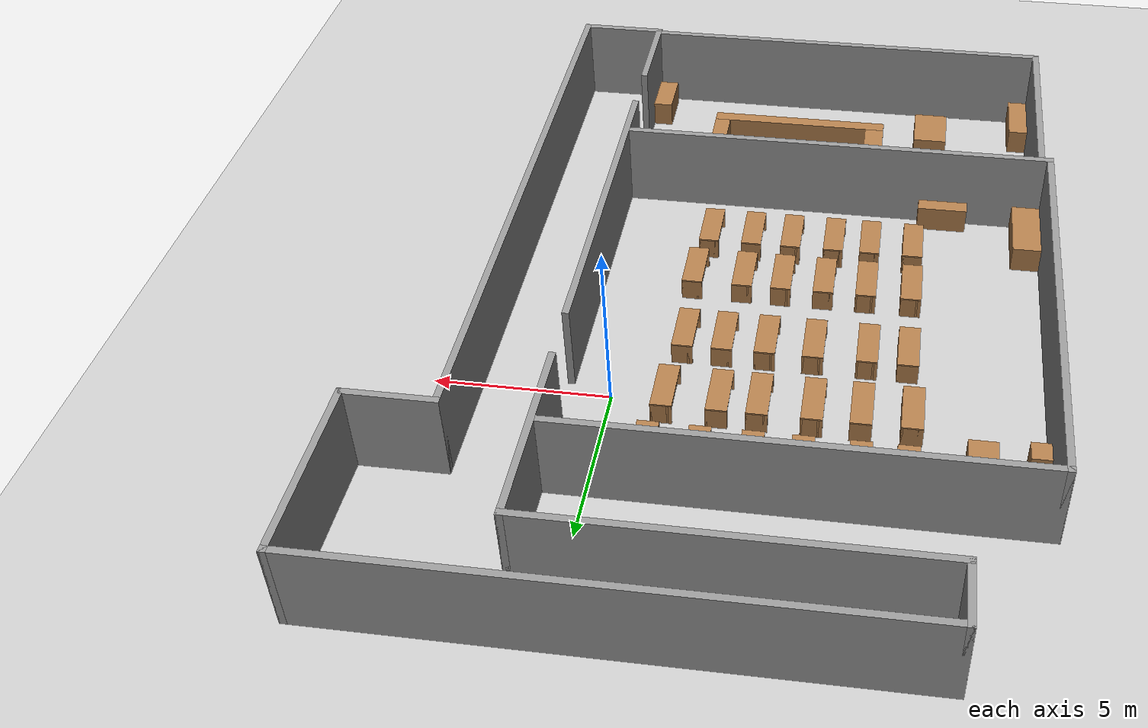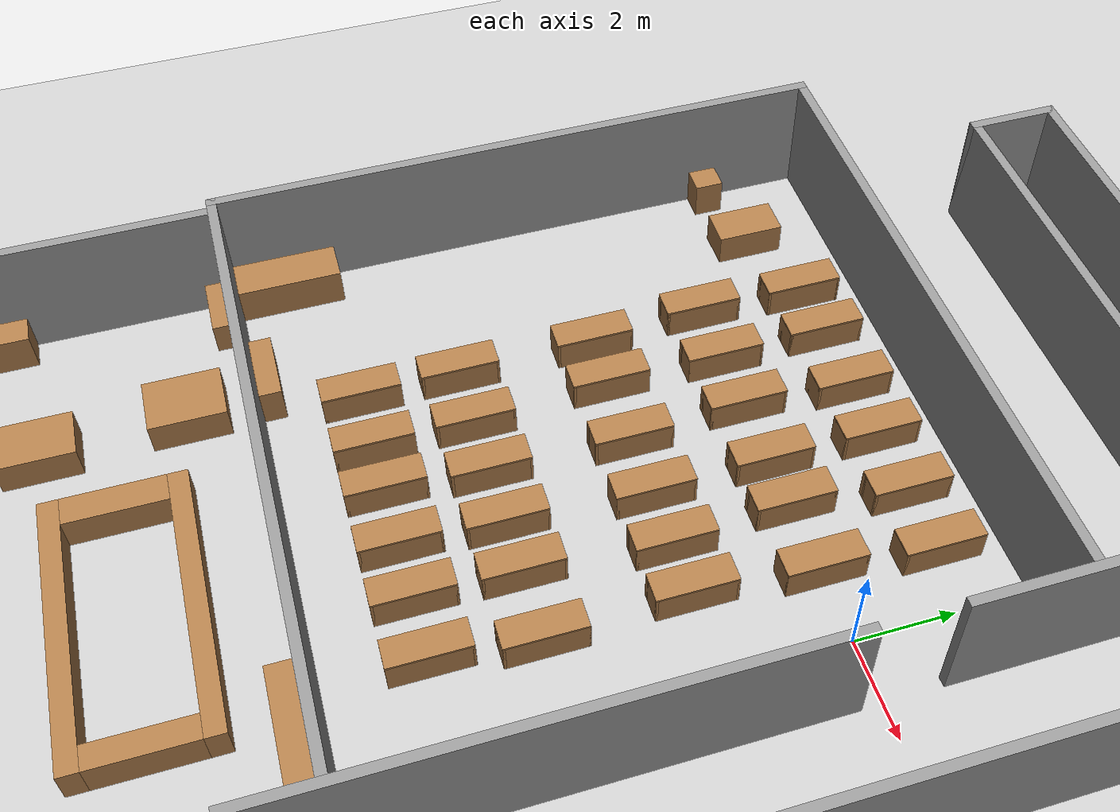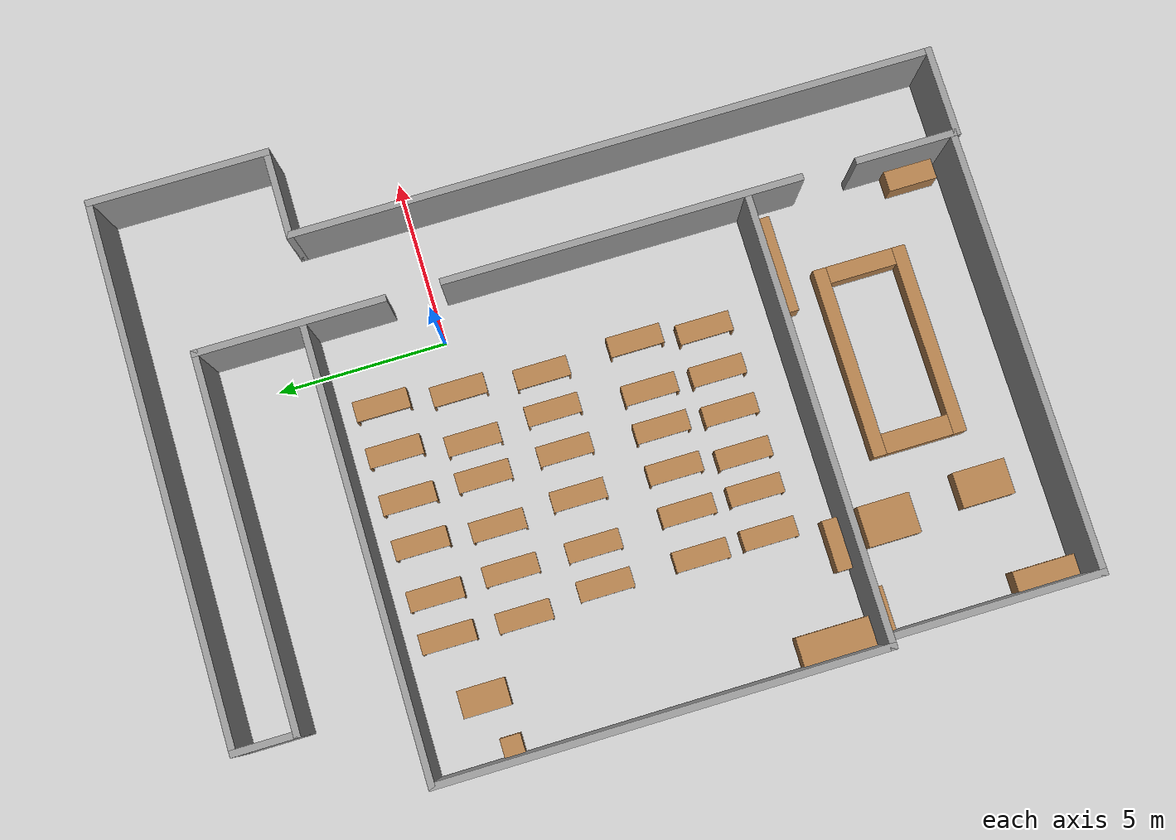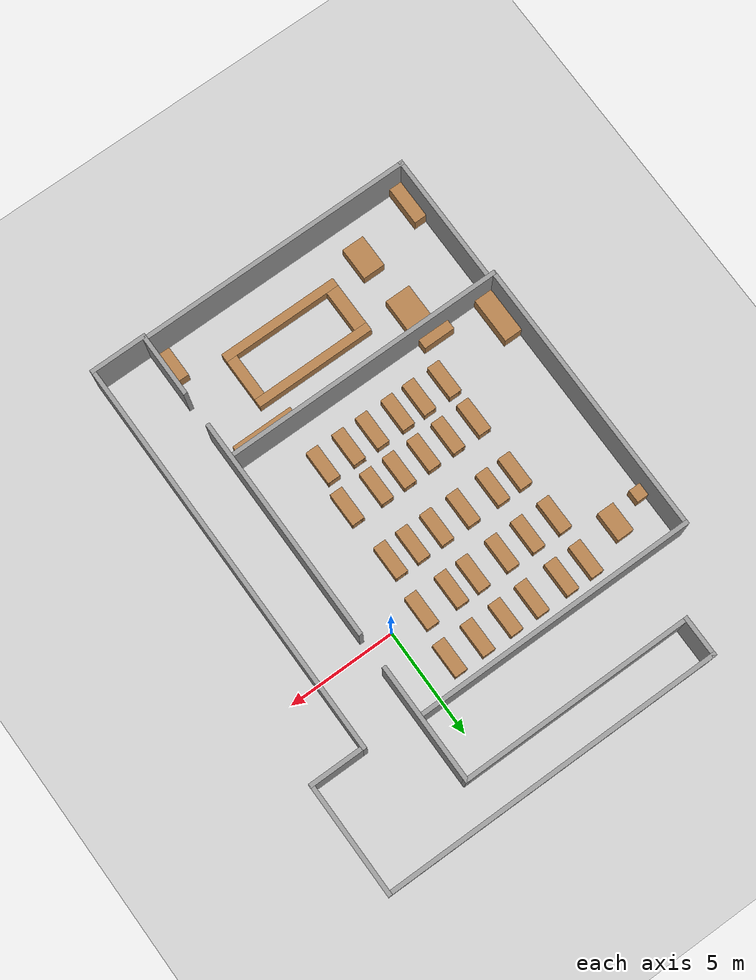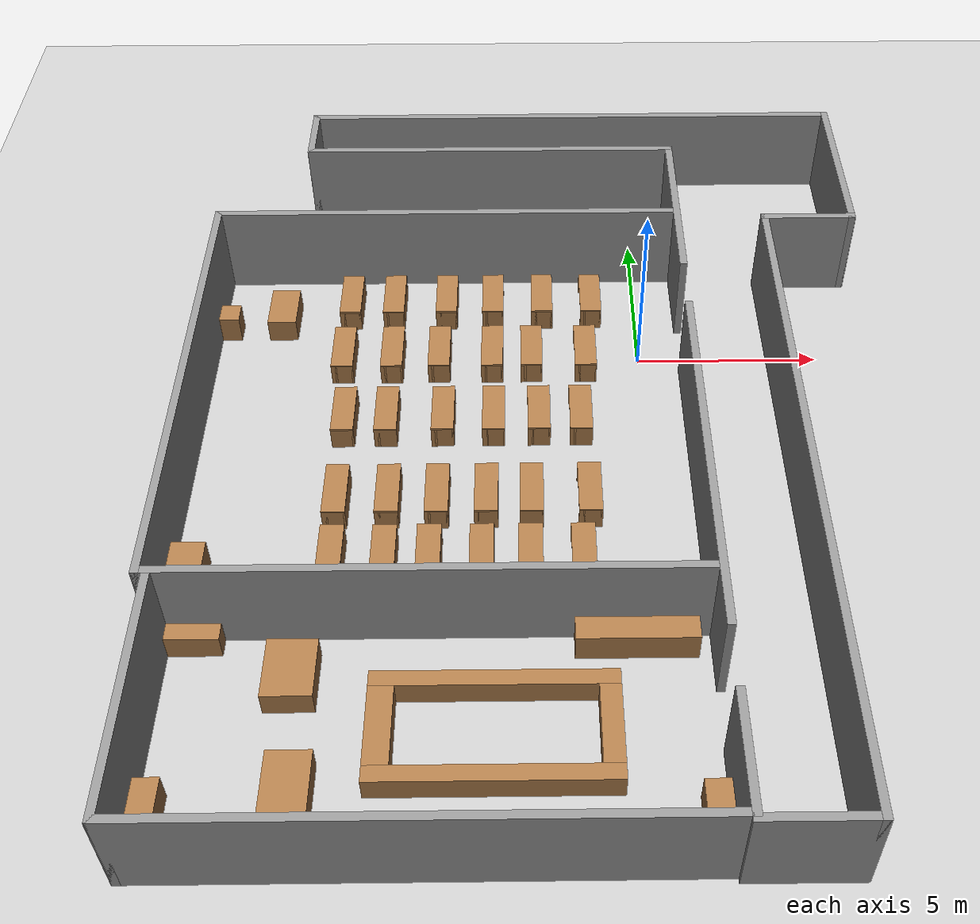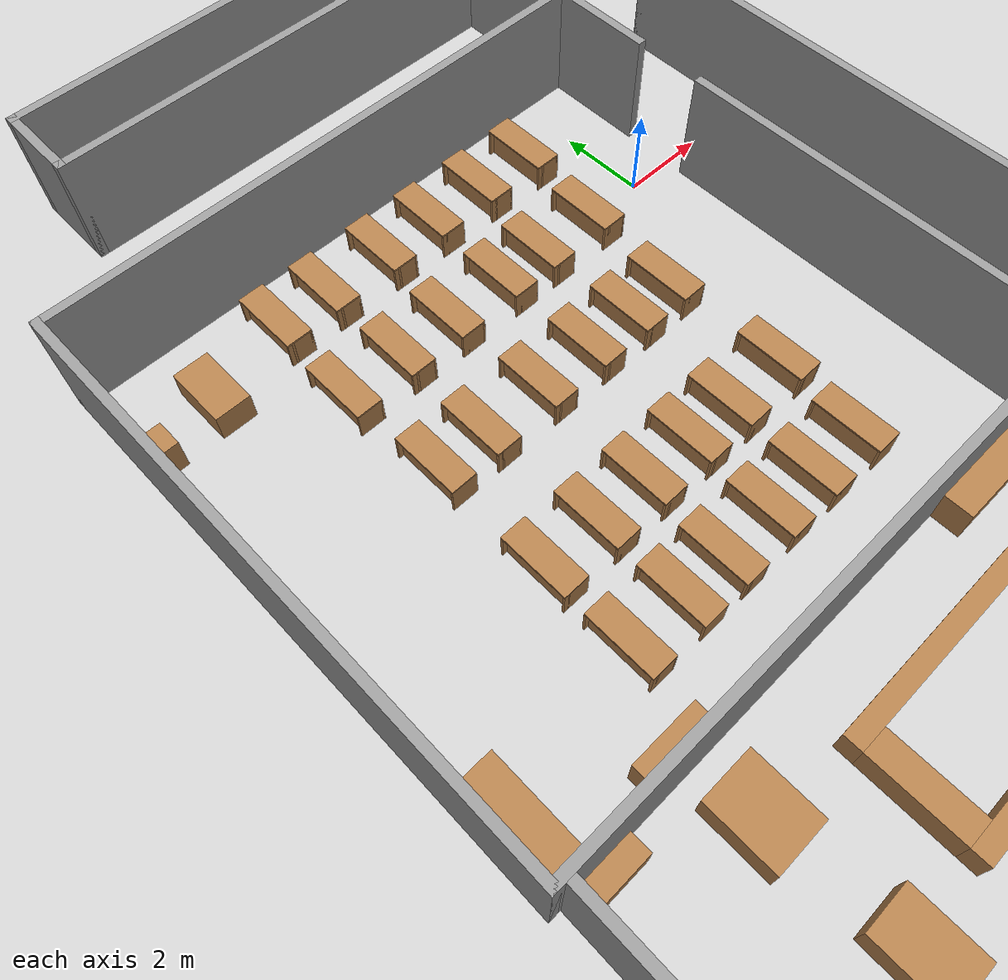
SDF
<sdf version="1.7">
 <world name="default">
  <light name="sun" type="directional">
   <pose>0 0 10 0 -0 0</pose>
   <diffuse>0.8 0.8 0.8 1</diffuse>
   <specular>0.2 0.2 0.2 1</specular>
   <attenuation>
    <range>1000</range>
    <constant>0.9</constant>
    <linear>0.01</linear>
    <quadratic>0.001</quadratic>
   </attenuation>
   <direction>-0.5 0.1 -0.9</direction>
   <spot><inner_angle>0</inner_angle><outer_angle>0</outer_angle><falloff>0</falloff></spot>
  </light>
  <model name="ground_plane">
   <static>1</static>
   <link name="link">
    <collision name="collision">
     <geometry><plane><normal>0 0 1</normal><size>100 100</size></plane></geometry>
     <surface><friction><ode><mu>100</mu><mu2>50</mu2></ode></friction></surface>
    </collision>
    <visual name="visual">
     <cast_shadows>0</cast_shadows>
     <geometry><plane><normal>0 0 1</normal><size>100 100</size></plane></geometry>
     <material>
      <script><uri>file://media/materials/scripts/gazebo.material</uri><name>Gazebo/Grey</name></script>
     </material>
    </visual>
   </link>
  </model>
  <physics name="default_physics" default="1" type="ode">
   <max_step_size>0.001</max_step_size>
   <real_time_factor>1</real_time_factor>
   <real_time_update_rate>1000</real_time_update_rate>
   <ode>
    <solver>
     <type>quick</type>
     <iters>100</iters>
     <sor>1</sor>
     <use_dynamic_moi_rescaling>0</use_dynamic_moi_rescaling>
    </solver>
    <constraints>
     <cfm>1e-05</cfm>
     <erp>0.2</erp>
     <contact_max_correcting_vel>0.2</contact_max_correcting_vel>
     <contact_surface_layer>0.001</contact_surface_layer>
    </constraints>
   </ode>
  </physics>
  <gravity>0 0 -9.8</gravity>
  <magnetic_field>6e-06 2.3e-05 -4.2e-05</magnetic_field>
  <atmosphere type="adiabatic"/>
  <scene><ambient>0.4 0.4 0.4 1</ambient><background>0.7 0.7 0.7 1</background><shadows>1</shadows></scene>
  <spherical_coordinates>
   <surface_model>EARTH_WGS84</surface_model>
   <latitude_deg>0</latitude_deg>
   <longitude_deg>0</longitude_deg>
   <elevation>0</elevation>
   <heading_deg>0</heading_deg>
  </spherical_coordinates>
  <model name="real_env">
   <static>1</static>
   <link name="building">
    <collision name="c_w0">
     <pose>1.200 -14.040 1.300 0 0 0</pose>
     <geometry><box><size>0.200 2.980 2.600</size></box></geometry>
    </collision>
    <visual name="v_w0">
     <pose>1.200 -14.040 1.300 0 0 0</pose>
     <geometry><box><size>0.200 2.980 2.600</size></box></geometry>
     <material>
      <script><uri>file://media/materials/scripts/gazebo.material</uri><name>Gazebo/Grey</name></script>
     </material>
    </visual>
    <collision name="c_w1">
     <pose>1.200 -5.700 1.300 0 0 0</pose>
     <geometry><box><size>0.200 10.600 2.600</size></box></geometry>
    </collision>
    <visual name="v_w1">
     <pose>1.200 -5.700 1.300 0 0 0</pose>
     <geometry><box><size>0.200 10.600 2.600</size></box></geometry>
     <material>
      <script><uri>file://media/materials/scripts/gazebo.material</uri><name>Gazebo/Grey</name></script>
     </material>
    </visual>
    <collision name="c_w2">
     <pose>1.200 3.950 1.300 0 0 0</pose>
     <geometry><box><size>0.200 5.600 2.600</size></box></geometry>
    </collision>
    <visual name="v_w2">
     <pose>1.200 3.950 1.300 0 0 0</pose>
     <geometry><box><size>0.200 5.600 2.600</size></box></geometry>
     <material>
      <script><uri>file://media/materials/scripts/gazebo.material</uri><name>Gazebo/Grey</name></script>
     </material>
    </visual>
    <collision name="c_w3">
     <pose>-11.950 -2.890 1.300 0 0 0</pose>
     <geometry><box><size>0.200 13.120 2.600</size></box></geometry>
    </collision>
    <visual name="v_w3">
     <pose>-11.950 -2.890 1.300 0 0 0</pose>
     <geometry><box><size>0.200 13.120 2.600</size></box></geometry>
     <material>
      <script><uri>file://media/materials/scripts/gazebo.material</uri><name>Gazebo/Grey</name></script>
     </material>
    </visual>
    <collision name="c_w4">
     <pose>-5.475 3.570 1.300 0 0 0</pose>
     <geometry><box><size>13.150 0.200 2.600</size></box></geometry>
    </collision>
    <visual name="v_w4">
     <pose>-5.475 3.570 1.300 0 0 0</pose>
     <geometry><box><size>13.150 0.200 2.600</size></box></geometry>
     <material>
      <script><uri>file://media/materials/scripts/gazebo.material</uri><name>Gazebo/Grey</name></script>
     </material>
    </visual>
    <collision name="c_w5">
     <pose>-5.475 -9.350 1.300 0 0 0</pose>
     <geometry><box><size>13.150 0.200 2.600</size></box></geometry>
    </collision>
    <visual name="v_w5">
     <pose>-5.475 -9.350 1.300 0 0 0</pose>
     <geometry><box><size>13.150 0.200 2.600</size></box></geometry>
     <material>
      <script><uri>file://media/materials/scripts/gazebo.material</uri><name>Gazebo/Grey</name></script>
     </material>
    </visual>
    <collision name="c_w6">
     <pose>-11.690 -12.490 1.300 0 0 0</pose>
     <geometry><box><size>0.200 6.080 2.600</size></box></geometry>
    </collision>
    <visual name="v_w6">
     <pose>-11.690 -12.490 1.300 0 0 0</pose>
     <geometry><box><size>0.200 6.080 2.600</size></box></geometry>
     <material>
      <script><uri>file://media/materials/scripts/gazebo.material</uri><name>Gazebo/Grey</name></script>
     </material>
    </visual>
    <collision name="c_w7">
     <pose>-5.345 -15.430 1.300 0 0 0</pose>
     <geometry><box><size>12.890 0.200 2.600</size></box></geometry>
    </collision>
    <visual name="v_w7">
     <pose>-5.345 -15.430 1.300 0 0 0</pose>
     <geometry><box><size>12.890 0.200 2.600</size></box></geometry>
     <material>
      <script><uri>file://media/materials/scripts/gazebo.material</uri><name>Gazebo/Grey</name></script>
     </material>
    </visual>
    <collision name="c_w8">
     <pose>-4.200 6.650 1.300 0 0 0</pose>
     <geometry><box><size>11.000 0.200 2.600</size></box></geometry>
    </collision>
    <visual name="v_w8">
     <pose>-4.200 6.650 1.300 0 0 0</pose>
     <geometry><box><size>11.000 0.200 2.600</size></box></geometry>
     <material>
      <script><uri>file://media/materials/scripts/gazebo.material</uri><name>Gazebo/Grey</name></script>
     </material>
    </visual>
    <collision name="c_w9">
     <pose>-9.600 7.530 1.300 0 0 0</pose>
     <geometry><box><size>0.200 1.960 2.600</size></box></geometry>
    </collision>
    <visual name="v_w9">
     <pose>-9.600 7.530 1.300 0 0 0</pose>
     <geometry><box><size>0.200 1.960 2.600</size></box></geometry>
     <material>
      <script><uri>file://media/materials/scripts/gazebo.material</uri><name>Gazebo/Grey</name></script>
     </material>
    </visual>
    <collision name="c_w10">
     <pose>-1.700 8.410 1.300 0 0 0</pose>
     <geometry><box><size>16.000 0.200 2.600</size></box></geometry>
    </collision>
    <visual name="v_w10">
     <pose>-1.700 8.410 1.300 0 0 0</pose>
     <geometry><box><size>16.000 0.200 2.600</size></box></geometry>
     <material>
      <script><uri>file://media/materials/scripts/gazebo.material</uri><name>Gazebo/Grey</name></script>
     </material>
    </visual>
    <collision name="c_w11">
     <pose>6.200 5.835 1.300 0 0 0</pose>
     <geometry><box><size>0.200 5.350 2.600</size></box></geometry>
    </collision>
    <visual name="v_w11">
     <pose>6.200 5.835 1.300 0 0 0</pose>
     <geometry><box><size>0.200 5.350 2.600</size></box></geometry>
     <material>
      <script><uri>file://media/materials/scripts/gazebo.material</uri><name>Gazebo/Grey</name></script>
     </material>
    </visual>
    <collision name="c_w12">
     <pose>2.450 -15.540 1.300 0 0 0</pose>
     <geometry><box><size>2.700 0.200 2.600</size></box></geometry>
    </collision>
    <visual name="v_w12">
     <pose>2.450 -15.540 1.300 0 0 0</pose>
     <geometry><box><size>2.700 0.200 2.600</size></box></geometry>
     <material>
      <script><uri>file://media/materials/scripts/gazebo.material</uri><name>Gazebo/Grey</name></script>
     </material>
    </visual>
    <collision name="c_w13">
     <pose>3.700 -6.140 1.300 0 0 0</pose>
     <geometry><box><size>0.200 19.000 2.600</size></box></geometry>
    </collision>
    <visual name="v_w13">
     <pose>3.700 -6.140 1.300 0 0 0</pose>
     <geometry><box><size>0.200 19.000 2.600</size></box></geometry>
     <material>
      <script><uri>file://media/materials/scripts/gazebo.material</uri><name>Gazebo/Grey</name></script>
     </material>
    </visual>
    <collision name="c_w14">
     <pose>4.950 3.260 1.300 0 0 0</pose>
     <geometry><box><size>2.700 0.200 2.600</size></box></geometry>
    </collision>
    <visual name="v_w14">
     <pose>4.950 3.260 1.300 0 0 0</pose>
     <geometry><box><size>2.700 0.200 2.600</size></box></geometry>
     <material>
      <script><uri>file://media/materials/scripts/gazebo.material</uri><name>Gazebo/Grey</name></script>
     </material>
    </visual>
    <collision name="c_c0">
     <pose>-8.850 -9.025 0.400 0 0 0</pose>
     <geometry><box><size>1.500 0.450 0.800</size></box></geometry>
    </collision>
    <visual name="v_c0">
     <pose>-8.850 -9.025 0.400 0 0 0</pose>
     <geometry><box><size>1.500 0.450 0.800</size></box></geometry>
     <material>
      <script><uri>file://media/materials/scripts/gazebo.material</uri><name>Gazebo/Wood</name></script>
     </material>
    </visual>
    <collision name="c_c1">
     <pose>-11.425 -8.175 0.400 0 0 0</pose>
     <geometry><box><size>0.850 2.150 0.800</size></box></geometry>
    </collision>
    <visual name="v_c1">
     <pose>-11.425 -8.175 0.400 0 0 0</pose>
     <geometry><box><size>0.850 2.150 0.800</size></box></geometry>
     <material>
      <script><uri>file://media/materials/scripts/gazebo.material</uri><name>Gazebo/Wood</name></script>
     </material>
    </visual>
    <collision name="c_c2">
     <pose>-11.575 1.300 0.400 0 0 0</pose>
     <geometry><box><size>0.550 0.600 0.800</size></box></geometry>
    </collision>
    <visual name="v_c2">
     <pose>-11.575 1.300 0.400 0 0 0</pose>
     <geometry><box><size>0.550 0.600 0.800</size></box></geometry>
     <material>
      <script><uri>file://media/materials/scripts/gazebo.material</uri><name>Gazebo/Wood</name></script>
     </material>
    </visual>
    <collision name="c_c3">
     <pose>-0.650 -9.755 0.400 0 0 0</pose>
     <geometry><box><size>2.900 0.610 0.800</size></box></geometry>
    </collision>
    <visual name="v_c3">
     <pose>-0.650 -9.755 0.400 0 0 0</pose>
     <geometry><box><size>2.900 0.610 0.800</size></box></geometry>
     <material>
      <script><uri>file://media/materials/scripts/gazebo.material</uri><name>Gazebo/Wood</name></script>
     </material>
    </visual>
    <collision name="c_c4">
     <pose>0.800 -14.380 0.400 0 0 0</pose>
     <geometry><box><size>0.600 1.440 0.800</size></box></geometry>
    </collision>
    <visual name="v_c4">
     <pose>0.800 -14.380 0.400 0 0 0</pose>
     <geometry><box><size>0.600 1.440 0.800</size></box></geometry>
     <material>
      <script><uri>file://media/materials/scripts/gazebo.material</uri><name>Gazebo/Wood</name></script>
     </material>
    </visual>
    <collision name="c_c5">
     <pose>-11.295 -14.415 0.400 0 0 0</pose>
     <geometry><box><size>0.590 1.830 0.800</size></box></geometry>
    </collision>
    <visual name="v_c5">
     <pose>-11.295 -14.415 0.400 0 0 0</pose>
     <geometry><box><size>0.590 1.830 0.800</size></box></geometry>
     <material>
      <script><uri>file://media/materials/scripts/gazebo.material</uri><name>Gazebo/Wood</name></script>
     </material>
    </visual>
    <collision name="c_t0">
     <pose>-10.100 1.700 0.340 0 0 0</pose>
     <geometry><box><size>0.800 1.400 0.680</size></box></geometry>
    </collision>
    <visual name="v_t0">
     <pose>-10.100 1.700 0.340 0 0 0</pose>
     <geometry><box><size>0.800 1.400 0.680</size></box></geometry>
     <material>
      <script><uri>file://media/materials/scripts/gazebo.material</uri><name>Gazebo/Wood</name></script>
     </material>
    </visual>
    <collision name="c_t1">
     <pose>-8.600 -10.675 0.340 0 0 0</pose>
     <geometry><box><size>1.200 1.550 0.680</size></box></geometry>
    </collision>
    <visual name="v_t1">
     <pose>-8.600 -10.675 0.340 0 0 0</pose>
     <geometry><box><size>1.200 1.550 0.680</size></box></geometry>
     <material>
      <script><uri>file://media/materials/scripts/gazebo.material</uri><name>Gazebo/Wood</name></script>
     </material>
    </visual>
    <collision name="c_t2">
     <pose>-8.375 -13.575 0.340 0 0 0</pose>
     <geometry><box><size>1.050 1.550 0.680</size></box></geometry>
    </collision>
    <visual name="v_t2">
     <pose>-8.375 -13.575 0.340 0 0 0</pose>
     <geometry><box><size>1.050 1.550 0.680</size></box></geometry>
     <material>
      <script><uri>file://media/materials/scripts/gazebo.material</uri><name>Gazebo/Wood</name></script>
     </material>
    </visual>
    <collision name="c_t3">
     <pose>-10.945 -9.675 0.340 0 0 0</pose>
     <geometry><box><size>1.290 0.450 0.680</size></box></geometry>
    </collision>
    <visual name="v_t3">
     <pose>-10.945 -9.675 0.340 0 0 0</pose>
     <geometry><box><size>1.290 0.450 0.680</size></box></geometry>
     <material>
      <script><uri>file://media/materials/scripts/gazebo.material</uri><name>Gazebo/Wood</name></script>
     </material>
    </visual>
    <collision name="c_t4">
     <pose>-3.950 -11.000 0.340 0 0 0</pose>
     <geometry><box><size>5.700 0.400 0.680</size></box></geometry>
    </collision>
    <visual name="v_t4">
     <pose>-3.950 -11.000 0.340 0 0 0</pose>
     <geometry><box><size>5.700 0.400 0.680</size></box></geometry>
     <material>
      <script><uri>file://media/materials/scripts/gazebo.material</uri><name>Gazebo/Wood</name></script>
     </material>
    </visual>
    <collision name="c_t5">
     <pose>-3.950 -13.400 0.340 0 0 0</pose>
     <geometry><box><size>5.700 0.400 0.680</size></box></geometry>
    </collision>
    <visual name="v_t5">
     <pose>-3.950 -13.400 0.340 0 0 0</pose>
     <geometry><box><size>5.700 0.400 0.680</size></box></geometry>
     <material>
      <script><uri>file://media/materials/scripts/gazebo.material</uri><name>Gazebo/Wood</name></script>
     </material>
    </visual>
    <collision name="c_t6">
     <pose>-6.500 -12.200 0.340 0 0 0</pose>
     <geometry><box><size>0.600 2.000 0.680</size></box></geometry>
    </collision>
    <visual name="v_t6">
     <pose>-6.500 -12.200 0.340 0 0 0</pose>
     <geometry><box><size>0.600 2.000 0.680</size></box></geometry>
     <material>
      <script><uri>file://media/materials/scripts/gazebo.material</uri><name>Gazebo/Wood</name></script>
     </material>
    </visual>
    <collision name="c_t7">
     <pose>-1.350 -12.200 0.340 0 0 0</pose>
     <geometry><box><size>0.500 2.000 0.680</size></box></geometry>
    </collision>
    <visual name="v_t7">
     <pose>-1.350 -12.200 0.340 0 0 0</pose>
     <geometry><box><size>0.500 2.000 0.680</size></box></geometry>
     <material>
      <script><uri>file://media/materials/scripts/gazebo.material</uri><name>Gazebo/Wood</name></script>
     </material>
    </visual>
    <collision name="c_d0">
     <pose>-8.190 2.220 0.660 0 0 0</pose>
     <geometry><box><size>0.600 1.600 0.040</size></box></geometry>
    </collision>
    <visual name="v_d0">
     <pose>-8.190 2.220 0.660 0 0 0</pose>
     <geometry><box><size>0.600 1.600 0.040</size></box></geometry>
     <material>
      <script><uri>file://media/materials/scripts/gazebo.material</uri><name>Gazebo/Wood</name></script>
     </material>
    </visual>
    <collision name="c_d0_p">
     <pose>-8.365 2.220 0.320 0 0 0</pose>
     <geometry><box><size>0.050 1.600 0.640</size></box></geometry>
    </collision>
    <visual name="v_d0_p">
     <pose>-8.365 2.220 0.320 0 0 0</pose>
     <geometry><box><size>0.050 1.600 0.640</size></box></geometry>
     <material>
      <script><uri>file://media/materials/scripts/gazebo.material</uri><name>Gazebo/Wood</name></script>
     </material>
    </visual>
    <collision name="c_d0_s">
     <pose>-8.190 1.445 0.320 0 0 0</pose>
     <geometry><box><size>0.600 0.050 0.640</size></box></geometry>
    </collision>
    <visual name="v_d0_s">
     <pose>-8.190 1.445 0.320 0 0 0</pose>
     <geometry><box><size>0.600 0.050 0.640</size></box></geometry>
     <material>
      <script><uri>file://media/materials/scripts/gazebo.material</uri><name>Gazebo/Wood</name></script>
     </material>
    </visual>
    <collision name="c_d0_n">
     <pose>-8.190 2.995 0.320 0 0 0</pose>
     <geometry><box><size>0.600 0.050 0.640</size></box></geometry>
    </collision>
    <visual name="v_d0_n">
     <pose>-8.190 2.995 0.320 0 0 0</pose>
     <geometry><box><size>0.600 0.050 0.640</size></box></geometry>
     <material>
      <script><uri>file://media/materials/scripts/gazebo.material</uri><name>Gazebo/Wood</name></script>
     </material>
    </visual>
    <collision name="c_d0_e">
     <pose>-7.915 2.220 0.320 0 0 0</pose>
     <geometry><box><size>0.050 1.600 0.640</size></box></geometry>
    </collision>
    <visual name="v_d0_e">
     <pose>-7.915 2.220 0.320 0 0 0</pose>
     <geometry><box><size>0.050 1.600 0.640</size></box></geometry>
     <material>
      <script><uri>file://media/materials/scripts/gazebo.material</uri><name>Gazebo/Wood</name></script>
     </material>
    </visual>
    <collision name="c_d1">
     <pose>-6.950 2.220 0.660 0 0 0</pose>
     <geometry><box><size>0.600 1.600 0.040</size></box></geometry>
    </collision>
    <visual name="v_d1">
     <pose>-6.950 2.220 0.660 0 0 0</pose>
     <geometry><box><size>0.600 1.600 0.040</size></box></geometry>
     <material>
      <script><uri>file://media/materials/scripts/gazebo.material</uri><name>Gazebo/Wood</name></script>
     </material>
    </visual>
    <collision name="c_d1_p">
     <pose>-7.125 2.220 0.320 0 0 0</pose>
     <geometry><box><size>0.050 1.600 0.640</size></box></geometry>
    </collision>
    <visual name="v_d1_p">
     <pose>-7.125 2.220 0.320 0 0 0</pose>
     <geometry><box><size>0.050 1.600 0.640</size></box></geometry>
     <material>
      <script><uri>file://media/materials/scripts/gazebo.material</uri><name>Gazebo/Wood</name></script>
     </material>
    </visual>
    <collision name="c_d1_s">
     <pose>-6.950 1.445 0.320 0 0 0</pose>
     <geometry><box><size>0.600 0.050 0.640</size></box></geometry>
    </collision>
    <visual name="v_d1_s">
     <pose>-6.950 1.445 0.320 0 0 0</pose>
     <geometry><box><size>0.600 0.050 0.640</size></box></geometry>
     <material>
      <script><uri>file://media/materials/scripts/gazebo.material</uri><name>Gazebo/Wood</name></script>
     </material>
    </visual>
    <collision name="c_d1_n">
     <pose>-6.950 2.995 0.320 0 0 0</pose>
     <geometry><box><size>0.600 0.050 0.640</size></box></geometry>
    </collision>
    <visual name="v_d1_n">
     <pose>-6.950 2.995 0.320 0 0 0</pose>
     <geometry><box><size>0.600 0.050 0.640</size></box></geometry>
     <material>
      <script><uri>file://media/materials/scripts/gazebo.material</uri><name>Gazebo/Wood</name></script>
     </material>
    </visual>
    <collision name="c_d1_e">
     <pose>-6.675 2.220 0.320 0 0 0</pose>
     <geometry><box><size>0.050 1.600 0.640</size></box></geometry>
    </collision>
    <visual name="v_d1_e">
     <pose>-6.675 2.220 0.320 0 0 0</pose>
     <geometry><box><size>0.050 1.600 0.640</size></box></geometry>
     <material>
      <script><uri>file://media/materials/scripts/gazebo.material</uri><name>Gazebo/Wood</name></script>
     </material>
    </visual>
    <collision name="c_d2">
     <pose>-5.440 2.220 0.660 0 0 0</pose>
     <geometry><box><size>0.600 1.600 0.040</size></box></geometry>
    </collision>
    <visual name="v_d2">
     <pose>-5.440 2.220 0.660 0 0 0</pose>
     <geometry><box><size>0.600 1.600 0.040</size></box></geometry>
     <material>
      <script><uri>file://media/materials/scripts/gazebo.material</uri><name>Gazebo/Wood</name></script>
     </material>
    </visual>
    <collision name="c_d2_p">
     <pose>-5.615 2.220 0.320 0 0 0</pose>
     <geometry><box><size>0.050 1.600 0.640</size></box></geometry>
    </collision>
    <visual name="v_d2_p">
     <pose>-5.615 2.220 0.320 0 0 0</pose>
     <geometry><box><size>0.050 1.600 0.640</size></box></geometry>
     <material>
      <script><uri>file://media/materials/scripts/gazebo.material</uri><name>Gazebo/Wood</name></script>
     </material>
    </visual>
    <collision name="c_d2_s">
     <pose>-5.440 1.445 0.320 0 0 0</pose>
     <geometry><box><size>0.600 0.050 0.640</size></box></geometry>
    </collision>
    <visual name="v_d2_s">
     <pose>-5.440 1.445 0.320 0 0 0</pose>
     <geometry><box><size>0.600 0.050 0.640</size></box></geometry>
     <material>
      <script><uri>file://media/materials/scripts/gazebo.material</uri><name>Gazebo/Wood</name></script>
     </material>
    </visual>
    <collision name="c_d2_n">
     <pose>-5.440 2.995 0.320 0 0 0</pose>
     <geometry><box><size>0.600 0.050 0.640</size></box></geometry>
    </collision>
    <visual name="v_d2_n">
     <pose>-5.440 2.995 0.320 0 0 0</pose>
     <geometry><box><size>0.600 0.050 0.640</size></box></geometry>
     <material>
      <script><uri>file://media/materials/scripts/gazebo.material</uri><name>Gazebo/Wood</name></script>
     </material>
    </visual>
    <collision name="c_d2_e">
     <pose>-5.165 2.220 0.320 0 0 0</pose>
     <geometry><box><size>0.050 1.600 0.640</size></box></geometry>
    </collision>
    <visual name="v_d2_e">
     <pose>-5.165 2.220 0.320 0 0 0</pose>
     <geometry><box><size>0.050 1.600 0.640</size></box></geometry>
     <material>
      <script><uri>file://media/materials/scripts/gazebo.material</uri><name>Gazebo/Wood</name></script>
     </material>
    </visual>
    <collision name="c_d3">
     <pose>-4.110 2.220 0.660 0 0 0</pose>
     <geometry><box><size>0.600 1.600 0.040</size></box></geometry>
    </collision>
    <visual name="v_d3">
     <pose>-4.110 2.220 0.660 0 0 0</pose>
     <geometry><box><size>0.600 1.600 0.040</size></box></geometry>
     <material>
      <script><uri>file://media/materials/scripts/gazebo.material</uri><name>Gazebo/Wood</name></script>
     </material>
    </visual>
    <collision name="c_d3_p">
     <pose>-4.285 2.220 0.320 0 0 0</pose>
     <geometry><box><size>0.050 1.600 0.640</size></box></geometry>
    </collision>
    <visual name="v_d3_p">
     <pose>-4.285 2.220 0.320 0 0 0</pose>
     <geometry><box><size>0.050 1.600 0.640</size></box></geometry>
     <material>
      <script><uri>file://media/materials/scripts/gazebo.material</uri><name>Gazebo/Wood</name></script>
     </material>
    </visual>
    <collision name="c_d3_s">
     <pose>-4.110 1.445 0.320 0 0 0</pose>
     <geometry><box><size>0.600 0.050 0.640</size></box></geometry>
    </collision>
    <visual name="v_d3_s">
     <pose>-4.110 1.445 0.320 0 0 0</pose>
     <geometry><box><size>0.600 0.050 0.640</size></box></geometry>
     <material>
      <script><uri>file://media/materials/scripts/gazebo.material</uri><name>Gazebo/Wood</name></script>
     </material>
    </visual>
    <collision name="c_d3_n">
     <pose>-4.110 2.995 0.320 0 0 0</pose>
     <geometry><box><size>0.600 0.050 0.640</size></box></geometry>
    </collision>
    <visual name="v_d3_n">
     <pose>-4.110 2.995 0.320 0 0 0</pose>
     <geometry><box><size>0.600 0.050 0.640</size></box></geometry>
     <material>
      <script><uri>file://media/materials/scripts/gazebo.material</uri><name>Gazebo/Wood</name></script>
     </material>
    </visual>
    <collision name="c_d3_e">
     <pose>-3.835 2.220 0.320 0 0 0</pose>
     <geometry><box><size>0.050 1.600 0.640</size></box></geometry>
    </collision>
    <visual name="v_d3_e">
     <pose>-3.835 2.220 0.320 0 0 0</pose>
     <geometry><box><size>0.050 1.600 0.640</size></box></geometry>
     <material>
      <script><uri>file://media/materials/scripts/gazebo.material</uri><name>Gazebo/Wood</name></script>
     </material>
    </visual>
    <collision name="c_d4">
     <pose>-2.700 2.220 0.660 0 0 0</pose>
     <geometry><box><size>0.600 1.600 0.040</size></box></geometry>
    </collision>
    <visual name="v_d4">
     <pose>-2.700 2.220 0.660 0 0 0</pose>
     <geometry><box><size>0.600 1.600 0.040</size></box></geometry>
     <material>
      <script><uri>file://media/materials/scripts/gazebo.material</uri><name>Gazebo/Wood</name></script>
     </material>
    </visual>
    <collision name="c_d4_p">
     <pose>-2.875 2.220 0.320 0 0 0</pose>
     <geometry><box><size>0.050 1.600 0.640</size></box></geometry>
    </collision>
    <visual name="v_d4_p">
     <pose>-2.875 2.220 0.320 0 0 0</pose>
     <geometry><box><size>0.050 1.600 0.640</size></box></geometry>
     <material>
      <script><uri>file://media/materials/scripts/gazebo.material</uri><name>Gazebo/Wood</name></script>
     </material>
    </visual>
    <collision name="c_d4_s">
     <pose>-2.700 1.445 0.320 0 0 0</pose>
     <geometry><box><size>0.600 0.050 0.640</size></box></geometry>
    </collision>
    <visual name="v_d4_s">
     <pose>-2.700 1.445 0.320 0 0 0</pose>
     <geometry><box><size>0.600 0.050 0.640</size></box></geometry>
     <material>
      <script><uri>file://media/materials/scripts/gazebo.material</uri><name>Gazebo/Wood</name></script>
     </material>
    </visual>
    <collision name="c_d4_n">
     <pose>-2.700 2.995 0.320 0 0 0</pose>
     <geometry><box><size>0.600 0.050 0.640</size></box></geometry>
    </collision>
    <visual name="v_d4_n">
     <pose>-2.700 2.995 0.320 0 0 0</pose>
     <geometry><box><size>0.600 0.050 0.640</size></box></geometry>
     <material>
      <script><uri>file://media/materials/scripts/gazebo.material</uri><name>Gazebo/Wood</name></script>
     </material>
    </visual>
    <collision name="c_d4_e">
     <pose>-2.425 2.220 0.320 0 0 0</pose>
     <geometry><box><size>0.050 1.600 0.640</size></box></geometry>
    </collision>
    <visual name="v_d4_e">
     <pose>-2.425 2.220 0.320 0 0 0</pose>
     <geometry><box><size>0.050 1.600 0.640</size></box></geometry>
     <material>
      <script><uri>file://media/materials/scripts/gazebo.material</uri><name>Gazebo/Wood</name></script>
     </material>
    </visual>
    <collision name="c_d5">
     <pose>-1.300 2.220 0.660 0 0 0</pose>
     <geometry><box><size>0.600 1.600 0.040</size></box></geometry>
    </collision>
    <visual name="v_d5">
     <pose>-1.300 2.220 0.660 0 0 0</pose>
     <geometry><box><size>0.600 1.600 0.040</size></box></geometry>
     <material>
      <script><uri>file://media/materials/scripts/gazebo.material</uri><name>Gazebo/Wood</name></script>
     </material>
    </visual>
    <collision name="c_d5_p">
     <pose>-1.475 2.220 0.320 0 0 0</pose>
     <geometry><box><size>0.050 1.600 0.640</size></box></geometry>
    </collision>
    <visual name="v_d5_p">
     <pose>-1.475 2.220 0.320 0 0 0</pose>
     <geometry><box><size>0.050 1.600 0.640</size></box></geometry>
     <material>
      <script><uri>file://media/materials/scripts/gazebo.material</uri><name>Gazebo/Wood</name></script>
     </material>
    </visual>
    <collision name="c_d5_s">
     <pose>-1.300 1.445 0.320 0 0 0</pose>
     <geometry><box><size>0.600 0.050 0.640</size></box></geometry>
    </collision>
    <visual name="v_d5_s">
     <pose>-1.300 1.445 0.320 0 0 0</pose>
     <geometry><box><size>0.600 0.050 0.640</size></box></geometry>
     <material>
      <script><uri>file://media/materials/scripts/gazebo.material</uri><name>Gazebo/Wood</name></script>
     </material>
    </visual>
    <collision name="c_d5_n">
     <pose>-1.300 2.995 0.320 0 0 0</pose>
     <geometry><box><size>0.600 0.050 0.640</size></box></geometry>
    </collision>
    <visual name="v_d5_n">
     <pose>-1.300 2.995 0.320 0 0 0</pose>
     <geometry><box><size>0.600 0.050 0.640</size></box></geometry>
     <material>
      <script><uri>file://media/materials/scripts/gazebo.material</uri><name>Gazebo/Wood</name></script>
     </material>
    </visual>
    <collision name="c_d5_e">
     <pose>-1.025 2.220 0.320 0 0 0</pose>
     <geometry><box><size>0.050 1.600 0.640</size></box></geometry>
    </collision>
    <visual name="v_d5_e">
     <pose>-1.025 2.220 0.320 0 0 0</pose>
     <geometry><box><size>0.050 1.600 0.640</size></box></geometry>
     <material>
      <script><uri>file://media/materials/scripts/gazebo.material</uri><name>Gazebo/Wood</name></script>
     </material>
    </visual>
    <collision name="c_d6">
     <pose>-8.250 -0.010 0.660 0 0 0</pose>
     <geometry><box><size>0.600 1.600 0.040</size></box></geometry>
    </collision>
    <visual name="v_d6">
     <pose>-8.250 -0.010 0.660 0 0 0</pose>
     <geometry><box><size>0.600 1.600 0.040</size></box></geometry>
     <material>
      <script><uri>file://media/materials/scripts/gazebo.material</uri><name>Gazebo/Wood</name></script>
     </material>
    </visual>
    <collision name="c_d6_p">
     <pose>-8.425 -0.010 0.320 0 0 0</pose>
     <geometry><box><size>0.050 1.600 0.640</size></box></geometry>
    </collision>
    <visual name="v_d6_p">
     <pose>-8.425 -0.010 0.320 0 0 0</pose>
     <geometry><box><size>0.050 1.600 0.640</size></box></geometry>
     <material>
      <script><uri>file://media/materials/scripts/gazebo.material</uri><name>Gazebo/Wood</name></script>
     </material>
    </visual>
    <collision name="c_d6_s">
     <pose>-8.250 -0.785 0.320 0 0 0</pose>
     <geometry><box><size>0.600 0.050 0.640</size></box></geometry>
    </collision>
    <visual name="v_d6_s">
     <pose>-8.250 -0.785 0.320 0 0 0</pose>
     <geometry><box><size>0.600 0.050 0.640</size></box></geometry>
     <material>
      <script><uri>file://media/materials/scripts/gazebo.material</uri><name>Gazebo/Wood</name></script>
     </material>
    </visual>
    <collision name="c_d6_n">
     <pose>-8.250 0.765 0.320 0 0 0</pose>
     <geometry><box><size>0.600 0.050 0.640</size></box></geometry>
    </collision>
    <visual name="v_d6_n">
     <pose>-8.250 0.765 0.320 0 0 0</pose>
     <geometry><box><size>0.600 0.050 0.640</size></box></geometry>
     <material>
      <script><uri>file://media/materials/scripts/gazebo.material</uri><name>Gazebo/Wood</name></script>
     </material>
    </visual>
    <collision name="c_d6_e">
     <pose>-7.975 -0.010 0.320 0 0 0</pose>
     <geometry><box><size>0.050 1.600 0.640</size></box></geometry>
    </collision>
    <visual name="v_d6_e">
     <pose>-7.975 -0.010 0.320 0 0 0</pose>
     <geometry><box><size>0.050 1.600 0.640</size></box></geometry>
     <material>
      <script><uri>file://media/materials/scripts/gazebo.material</uri><name>Gazebo/Wood</name></script>
     </material>
    </visual>
    <collision name="c_d7">
     <pose>-6.890 -0.010 0.660 0 0 0</pose>
     <geometry><box><size>0.600 1.600 0.040</size></box></geometry>
    </collision>
    <visual name="v_d7">
     <pose>-6.890 -0.010 0.660 0 0 0</pose>
     <geometry><box><size>0.600 1.600 0.040</size></box></geometry>
     <material>
      <script><uri>file://media/materials/scripts/gazebo.material</uri><name>Gazebo/Wood</name></script>
     </material>
    </visual>
    <collision name="c_d7_p">
     <pose>-7.065 -0.010 0.320 0 0 0</pose>
     <geometry><box><size>0.050 1.600 0.640</size></box></geometry>
    </collision>
    <visual name="v_d7_p">
     <pose>-7.065 -0.010 0.320 0 0 0</pose>
     <geometry><box><size>0.050 1.600 0.640</size></box></geometry>
     <material>
      <script><uri>file://media/materials/scripts/gazebo.material</uri><name>Gazebo/Wood</name></script>
     </material>
    </visual>
    <collision name="c_d7_s">
     <pose>-6.890 -0.785 0.320 0 0 0</pose>
     <geometry><box><size>0.600 0.050 0.640</size></box></geometry>
    </collision>
    <visual name="v_d7_s">
     <pose>-6.890 -0.785 0.320 0 0 0</pose>
     <geometry><box><size>0.600 0.050 0.640</size></box></geometry>
     <material>
      <script><uri>file://media/materials/scripts/gazebo.material</uri><name>Gazebo/Wood</name></script>
     </material>
    </visual>
    <collision name="c_d7_n">
     <pose>-6.890 0.765 0.320 0 0 0</pose>
     <geometry><box><size>0.600 0.050 0.640</size></box></geometry>
    </collision>
    <visual name="v_d7_n">
     <pose>-6.890 0.765 0.320 0 0 0</pose>
     <geometry><box><size>0.600 0.050 0.640</size></box></geometry>
     <material>
      <script><uri>file://media/materials/scripts/gazebo.material</uri><name>Gazebo/Wood</name></script>
     </material>
    </visual>
    <collision name="c_d7_e">
     <pose>-6.615 -0.010 0.320 0 0 0</pose>
     <geometry><box><size>0.050 1.600 0.640</size></box></geometry>
    </collision>
    <visual name="v_d7_e">
     <pose>-6.615 -0.010 0.320 0 0 0</pose>
     <geometry><box><size>0.050 1.600 0.640</size></box></geometry>
     <material>
      <script><uri>file://media/materials/scripts/gazebo.material</uri><name>Gazebo/Wood</name></script>
     </material>
    </visual>
    <collision name="c_d8">
     <pose>-5.580 -0.010 0.660 0 0 0</pose>
     <geometry><box><size>0.600 1.600 0.040</size></box></geometry>
    </collision>
    <visual name="v_d8">
     <pose>-5.580 -0.010 0.660 0 0 0</pose>
     <geometry><box><size>0.600 1.600 0.040</size></box></geometry>
     <material>
      <script><uri>file://media/materials/scripts/gazebo.material</uri><name>Gazebo/Wood</name></script>
     </material>
    </visual>
    <collision name="c_d8_p">
     <pose>-5.755 -0.010 0.320 0 0 0</pose>
     <geometry><box><size>0.050 1.600 0.640</size></box></geometry>
    </collision>
    <visual name="v_d8_p">
     <pose>-5.755 -0.010 0.320 0 0 0</pose>
     <geometry><box><size>0.050 1.600 0.640</size></box></geometry>
     <material>
      <script><uri>file://media/materials/scripts/gazebo.material</uri><name>Gazebo/Wood</name></script>
     </material>
    </visual>
    <collision name="c_d8_s">
     <pose>-5.580 -0.785 0.320 0 0 0</pose>
     <geometry><box><size>0.600 0.050 0.640</size></box></geometry>
    </collision>
    <visual name="v_d8_s">
     <pose>-5.580 -0.785 0.320 0 0 0</pose>
     <geometry><box><size>0.600 0.050 0.640</size></box></geometry>
     <material>
      <script><uri>file://media/materials/scripts/gazebo.material</uri><name>Gazebo/Wood</name></script>
     </material>
    </visual>
    <collision name="c_d8_n">
     <pose>-5.580 0.765 0.320 0 0 0</pose>
     <geometry><box><size>0.600 0.050 0.640</size></box></geometry>
    </collision>
    <visual name="v_d8_n">
     <pose>-5.580 0.765 0.320 0 0 0</pose>
     <geometry><box><size>0.600 0.050 0.640</size></box></geometry>
     <material>
      <script><uri>file://media/materials/scripts/gazebo.material</uri><name>Gazebo/Wood</name></script>
     </material>
    </visual>
    <collision name="c_d8_e">
     <pose>-5.305 -0.010 0.320 0 0 0</pose>
     <geometry><box><size>0.050 1.600 0.640</size></box></geometry>
    </collision>
    <visual name="v_d8_e">
     <pose>-5.305 -0.010 0.320 0 0 0</pose>
     <geometry><box><size>0.050 1.600 0.640</size></box></geometry>
     <material>
      <script><uri>file://media/materials/scripts/gazebo.material</uri><name>Gazebo/Wood</name></script>
     </material>
    </visual>
    <collision name="c_d9">
     <pose>-4.110 -0.010 0.660 0 0 0</pose>
     <geometry><box><size>0.600 1.600 0.040</size></box></geometry>
    </collision>
    <visual name="v_d9">
     <pose>-4.110 -0.010 0.660 0 0 0</pose>
     <geometry><box><size>0.600 1.600 0.040</size></box></geometry>
     <material>
      <script><uri>file://media/materials/scripts/gazebo.material</uri><name>Gazebo/Wood</name></script>
     </material>
    </visual>
    <collision name="c_d9_p">
     <pose>-4.285 -0.010 0.320 0 0 0</pose>
     <geometry><box><size>0.050 1.600 0.640</size></box></geometry>
    </collision>
    <visual name="v_d9_p">
     <pose>-4.285 -0.010 0.320 0 0 0</pose>
     <geometry><box><size>0.050 1.600 0.640</size></box></geometry>
     <material>
      <script><uri>file://media/materials/scripts/gazebo.material</uri><name>Gazebo/Wood</name></script>
     </material>
    </visual>
    <collision name="c_d9_s">
     <pose>-4.110 -0.785 0.320 0 0 0</pose>
     <geometry><box><size>0.600 0.050 0.640</size></box></geometry>
    </collision>
    <visual name="v_d9_s">
     <pose>-4.110 -0.785 0.320 0 0 0</pose>
     <geometry><box><size>0.600 0.050 0.640</size></box></geometry>
     <material>
      <script><uri>file://media/materials/scripts/gazebo.material</uri><name>Gazebo/Wood</name></script>
     </material>
    </visual>
    <collision name="c_d9_n">
     <pose>-4.110 0.765 0.320 0 0 0</pose>
     <geometry><box><size>0.600 0.050 0.640</size></box></geometry>
    </collision>
    <visual name="v_d9_n">
     <pose>-4.110 0.765 0.320 0 0 0</pose>
     <geometry><box><size>0.600 0.050 0.640</size></box></geometry>
     <material>
      <script><uri>file://media/materials/scripts/gazebo.material</uri><name>Gazebo/Wood</name></script>
     </material>
    </visual>
    <collision name="c_d9_e">
     <pose>-3.835 -0.010 0.320 0 0 0</pose>
     <geometry><box><size>0.050 1.600 0.640</size></box></geometry>
    </collision>
    <visual name="v_d9_e">
     <pose>-3.835 -0.010 0.320 0 0 0</pose>
     <geometry><box><size>0.050 1.600 0.640</size></box></geometry>
     <material>
      <script><uri>file://media/materials/scripts/gazebo.material</uri><name>Gazebo/Wood</name></script>
     </material>
    </visual>
    <collision name="c_d10">
     <pose>-3.020 -0.010 0.660 0 0 0</pose>
     <geometry><box><size>0.600 1.600 0.040</size></box></geometry>
    </collision>
    <visual name="v_d10">
     <pose>-3.020 -0.010 0.660 0 0 0</pose>
     <geometry><box><size>0.600 1.600 0.040</size></box></geometry>
     <material>
      <script><uri>file://media/materials/scripts/gazebo.material</uri><name>Gazebo/Wood</name></script>
     </material>
    </visual>
    <collision name="c_d10_p">
     <pose>-3.195 -0.010 0.320 0 0 0</pose>
     <geometry><box><size>0.050 1.600 0.640</size></box></geometry>
    </collision>
    <visual name="v_d10_p">
     <pose>-3.195 -0.010 0.320 0 0 0</pose>
     <geometry><box><size>0.050 1.600 0.640</size></box></geometry>
     <material>
      <script><uri>file://media/materials/scripts/gazebo.material</uri><name>Gazebo/Wood</name></script>
     </material>
    </visual>
    <collision name="c_d10_s">
     <pose>-3.020 -0.785 0.320 0 0 0</pose>
     <geometry><box><size>0.600 0.050 0.640</size></box></geometry>
    </collision>
    <visual name="v_d10_s">
     <pose>-3.020 -0.785 0.320 0 0 0</pose>
     <geometry><box><size>0.600 0.050 0.640</size></box></geometry>
     <material>
      <script><uri>file://media/materials/scripts/gazebo.material</uri><name>Gazebo/Wood</name></script>
     </material>
    </visual>
    <collision name="c_d10_n">
     <pose>-3.020 0.765 0.320 0 0 0</pose>
     <geometry><box><size>0.600 0.050 0.640</size></box></geometry>
    </collision>
    <visual name="v_d10_n">
     <pose>-3.020 0.765 0.320 0 0 0</pose>
     <geometry><box><size>0.600 0.050 0.640</size></box></geometry>
     <material>
      <script><uri>file://media/materials/scripts/gazebo.material</uri><name>Gazebo/Wood</name></script>
     </material>
    </visual>
    <collision name="c_d10_e">
     <pose>-2.745 -0.010 0.320 0 0 0</pose>
     <geometry><box><size>0.050 1.600 0.640</size></box></geometry>
    </collision>
    <visual name="v_d10_e">
     <pose>-2.745 -0.010 0.320 0 0 0</pose>
     <geometry><box><size>0.050 1.600 0.640</size></box></geometry>
     <material>
      <script><uri>file://media/materials/scripts/gazebo.material</uri><name>Gazebo/Wood</name></script>
     </material>
    </visual>
    <collision name="c_d11">
     <pose>-1.520 -0.010 0.660 0 0 0</pose>
     <geometry><box><size>0.600 1.600 0.040</size></box></geometry>
    </collision>
    <visual name="v_d11">
     <pose>-1.520 -0.010 0.660 0 0 0</pose>
     <geometry><box><size>0.600 1.600 0.040</size></box></geometry>
     <material>
      <script><uri>file://media/materials/scripts/gazebo.material</uri><name>Gazebo/Wood</name></script>
     </material>
    </visual>
    <collision name="c_d11_p">
     <pose>-1.695 -0.010 0.320 0 0 0</pose>
     <geometry><box><size>0.050 1.600 0.640</size></box></geometry>
    </collision>
    <visual name="v_d11_p">
     <pose>-1.695 -0.010 0.320 0 0 0</pose>
     <geometry><box><size>0.050 1.600 0.640</size></box></geometry>
     <material>
      <script><uri>file://media/materials/scripts/gazebo.material</uri><name>Gazebo/Wood</name></script>
     </material>
    </visual>
    <collision name="c_d11_s">
     <pose>-1.520 -0.785 0.320 0 0 0</pose>
     <geometry><box><size>0.600 0.050 0.640</size></box></geometry>
    </collision>
    <visual name="v_d11_s">
     <pose>-1.520 -0.785 0.320 0 0 0</pose>
     <geometry><box><size>0.600 0.050 0.640</size></box></geometry>
     <material>
      <script><uri>file://media/materials/scripts/gazebo.material</uri><name>Gazebo/Wood</name></script>
     </material>
    </visual>
    <collision name="c_d11_n">
     <pose>-1.520 0.765 0.320 0 0 0</pose>
     <geometry><box><size>0.600 0.050 0.640</size></box></geometry>
    </collision>
    <visual name="v_d11_n">
     <pose>-1.520 0.765 0.320 0 0 0</pose>
     <geometry><box><size>0.600 0.050 0.640</size></box></geometry>
     <material>
      <script><uri>file://media/materials/scripts/gazebo.material</uri><name>Gazebo/Wood</name></script>
     </material>
    </visual>
    <collision name="c_d11_e">
     <pose>-1.245 -0.010 0.320 0 0 0</pose>
     <geometry><box><size>0.050 1.600 0.640</size></box></geometry>
    </collision>
    <visual name="v_d11_e">
     <pose>-1.245 -0.010 0.320 0 0 0</pose>
     <geometry><box><size>0.050 1.600 0.640</size></box></geometry>
     <material>
      <script><uri>file://media/materials/scripts/gazebo.material</uri><name>Gazebo/Wood</name></script>
     </material>
    </visual>
    <collision name="c_d12">
     <pose>-8.050 -2.440 0.660 0 0 0</pose>
     <geometry><box><size>0.600 1.600 0.040</size></box></geometry>
    </collision>
    <visual name="v_d12">
     <pose>-8.050 -2.440 0.660 0 0 0</pose>
     <geometry><box><size>0.600 1.600 0.040</size></box></geometry>
     <material>
      <script><uri>file://media/materials/scripts/gazebo.material</uri><name>Gazebo/Wood</name></script>
     </material>
    </visual>
    <collision name="c_d12_p">
     <pose>-8.225 -2.440 0.320 0 0 0</pose>
     <geometry><box><size>0.050 1.600 0.640</size></box></geometry>
    </collision>
    <visual name="v_d12_p">
     <pose>-8.225 -2.440 0.320 0 0 0</pose>
     <geometry><box><size>0.050 1.600 0.640</size></box></geometry>
     <material>
      <script><uri>file://media/materials/scripts/gazebo.material</uri><name>Gazebo/Wood</name></script>
     </material>
    </visual>
    <collision name="c_d12_s">
     <pose>-8.050 -3.215 0.320 0 0 0</pose>
     <geometry><box><size>0.600 0.050 0.640</size></box></geometry>
    </collision>
    <visual name="v_d12_s">
     <pose>-8.050 -3.215 0.320 0 0 0</pose>
     <geometry><box><size>0.600 0.050 0.640</size></box></geometry>
     <material>
      <script><uri>file://media/materials/scripts/gazebo.material</uri><name>Gazebo/Wood</name></script>
     </material>
    </visual>
    <collision name="c_d12_n">
     <pose>-8.050 -1.665 0.320 0 0 0</pose>
     <geometry><box><size>0.600 0.050 0.640</size></box></geometry>
    </collision>
    <visual name="v_d12_n">
     <pose>-8.050 -1.665 0.320 0 0 0</pose>
     <geometry><box><size>0.600 0.050 0.640</size></box></geometry>
     <material>
      <script><uri>file://media/materials/scripts/gazebo.material</uri><name>Gazebo/Wood</name></script>
     </material>
    </visual>
    <collision name="c_d12_e">
     <pose>-7.775 -2.440 0.320 0 0 0</pose>
     <geometry><box><size>0.050 1.600 0.640</size></box></geometry>
    </collision>
    <visual name="v_d12_e">
     <pose>-7.775 -2.440 0.320 0 0 0</pose>
     <geometry><box><size>0.050 1.600 0.640</size></box></geometry>
     <material>
      <script><uri>file://media/materials/scripts/gazebo.material</uri><name>Gazebo/Wood</name></script>
     </material>
    </visual>
    <collision name="c_d13">
     <pose>-6.910 -2.440 0.660 0 0 0</pose>
     <geometry><box><size>0.600 1.600 0.040</size></box></geometry>
    </collision>
    <visual name="v_d13">
     <pose>-6.910 -2.440 0.660 0 0 0</pose>
     <geometry><box><size>0.600 1.600 0.040</size></box></geometry>
     <material>
      <script><uri>file://media/materials/scripts/gazebo.material</uri><name>Gazebo/Wood</name></script>
     </material>
    </visual>
    <collision name="c_d13_p">
     <pose>-7.085 -2.440 0.320 0 0 0</pose>
     <geometry><box><size>0.050 1.600 0.640</size></box></geometry>
    </collision>
    <visual name="v_d13_p">
     <pose>-7.085 -2.440 0.320 0 0 0</pose>
     <geometry><box><size>0.050 1.600 0.640</size></box></geometry>
     <material>
      <script><uri>file://media/materials/scripts/gazebo.material</uri><name>Gazebo/Wood</name></script>
     </material>
    </visual>
    <collision name="c_d13_s">
     <pose>-6.910 -3.215 0.320 0 0 0</pose>
     <geometry><box><size>0.600 0.050 0.640</size></box></geometry>
    </collision>
    <visual name="v_d13_s">
     <pose>-6.910 -3.215 0.320 0 0 0</pose>
     <geometry><box><size>0.600 0.050 0.640</size></box></geometry>
     <material>
      <script><uri>file://media/materials/scripts/gazebo.material</uri><name>Gazebo/Wood</name></script>
     </material>
    </visual>
    <collision name="c_d13_n">
     <pose>-6.910 -1.665 0.320 0 0 0</pose>
     <geometry><box><size>0.600 0.050 0.640</size></box></geometry>
    </collision>
    <visual name="v_d13_n">
     <pose>-6.910 -1.665 0.320 0 0 0</pose>
     <geometry><box><size>0.600 0.050 0.640</size></box></geometry>
     <material>
      <script><uri>file://media/materials/scripts/gazebo.material</uri><name>Gazebo/Wood</name></script>
     </material>
    </visual>
    <collision name="c_d13_e">
     <pose>-6.635 -2.440 0.320 0 0 0</pose>
     <geometry><box><size>0.050 1.600 0.640</size></box></geometry>
    </collision>
    <visual name="v_d13_e">
     <pose>-6.635 -2.440 0.320 0 0 0</pose>
     <geometry><box><size>0.050 1.600 0.640</size></box></geometry>
     <material>
      <script><uri>file://media/materials/scripts/gazebo.material</uri><name>Gazebo/Wood</name></script>
     </material>
    </visual>
    <collision name="c_d14">
     <pose>-5.400 -2.440 0.660 0 0 0</pose>
     <geometry><box><size>0.600 1.600 0.040</size></box></geometry>
    </collision>
    <visual name="v_d14">
     <pose>-5.400 -2.440 0.660 0 0 0</pose>
     <geometry><box><size>0.600 1.600 0.040</size></box></geometry>
     <material>
      <script><uri>file://media/materials/scripts/gazebo.material</uri><name>Gazebo/Wood</name></script>
     </material>
    </visual>
    <collision name="c_d14_p">
     <pose>-5.575 -2.440 0.320 0 0 0</pose>
     <geometry><box><size>0.050 1.600 0.640</size></box></geometry>
    </collision>
    <visual name="v_d14_p">
     <pose>-5.575 -2.440 0.320 0 0 0</pose>
     <geometry><box><size>0.050 1.600 0.640</size></box></geometry>
     <material>
      <script><uri>file://media/materials/scripts/gazebo.material</uri><name>Gazebo/Wood</name></script>
     </material>
    </visual>
    <collision name="c_d14_s">
     <pose>-5.400 -3.215 0.320 0 0 0</pose>
     <geometry><box><size>0.600 0.050 0.640</size></box></geometry>
    </collision>
    <visual name="v_d14_s">
     <pose>-5.400 -3.215 0.320 0 0 0</pose>
     <geometry><box><size>0.600 0.050 0.640</size></box></geometry>
     <material>
      <script><uri>file://media/materials/scripts/gazebo.material</uri><name>Gazebo/Wood</name></script>
     </material>
    </visual>
    <collision name="c_d14_n">
     <pose>-5.400 -1.665 0.320 0 0 0</pose>
     <geometry><box><size>0.600 0.050 0.640</size></box></geometry>
    </collision>
    <visual name="v_d14_n">
     <pose>-5.400 -1.665 0.320 0 0 0</pose>
     <geometry><box><size>0.600 0.050 0.640</size></box></geometry>
     <material>
      <script><uri>file://media/materials/scripts/gazebo.material</uri><name>Gazebo/Wood</name></script>
     </material>
    </visual>
    <collision name="c_d14_e">
     <pose>-5.125 -2.440 0.320 0 0 0</pose>
     <geometry><box><size>0.050 1.600 0.640</size></box></geometry>
    </collision>
    <visual name="v_d14_e">
     <pose>-5.125 -2.440 0.320 0 0 0</pose>
     <geometry><box><size>0.050 1.600 0.640</size></box></geometry>
     <material>
      <script><uri>file://media/materials/scripts/gazebo.material</uri><name>Gazebo/Wood</name></script>
     </material>
    </visual>
    <collision name="c_d15">
     <pose>-4.050 -2.440 0.660 0 0 0</pose>
     <geometry><box><size>0.600 1.600 0.040</size></box></geometry>
    </collision>
    <visual name="v_d15">
     <pose>-4.050 -2.440 0.660 0 0 0</pose>
     <geometry><box><size>0.600 1.600 0.040</size></box></geometry>
     <material>
      <script><uri>file://media/materials/scripts/gazebo.material</uri><name>Gazebo/Wood</name></script>
     </material>
    </visual>
    <collision name="c_d15_p">
     <pose>-4.225 -2.440 0.320 0 0 0</pose>
     <geometry><box><size>0.050 1.600 0.640</size></box></geometry>
    </collision>
    <visual name="v_d15_p">
     <pose>-4.225 -2.440 0.320 0 0 0</pose>
     <geometry><box><size>0.050 1.600 0.640</size></box></geometry>
     <material>
      <script><uri>file://media/materials/scripts/gazebo.material</uri><name>Gazebo/Wood</name></script>
     </material>
    </visual>
    <collision name="c_d15_s">
     <pose>-4.050 -3.215 0.320 0 0 0</pose>
     <geometry><box><size>0.600 0.050 0.640</size></box></geometry>
    </collision>
    <visual name="v_d15_s">
     <pose>-4.050 -3.215 0.320 0 0 0</pose>
     <geometry><box><size>0.600 0.050 0.640</size></box></geometry>
     <material>
      <script><uri>file://media/materials/scripts/gazebo.material</uri><name>Gazebo/Wood</name></script>
     </material>
    </visual>
    <collision name="c_d15_n">
     <pose>-4.050 -1.665 0.320 0 0 0</pose>
     <geometry><box><size>0.600 0.050 0.640</size></box></geometry>
    </collision>
    <visual name="v_d15_n">
     <pose>-4.050 -1.665 0.320 0 0 0</pose>
     <geometry><box><size>0.600 0.050 0.640</size></box></geometry>
     <material>
      <script><uri>file://media/materials/scripts/gazebo.material</uri><name>Gazebo/Wood</name></script>
     </material>
    </visual>
    <collision name="c_d15_e">
     <pose>-3.775 -2.440 0.320 0 0 0</pose>
     <geometry><box><size>0.050 1.600 0.640</size></box></geometry>
    </collision>
    <visual name="v_d15_e">
     <pose>-3.775 -2.440 0.320 0 0 0</pose>
     <geometry><box><size>0.050 1.600 0.640</size></box></geometry>
     <material>
      <script><uri>file://media/materials/scripts/gazebo.material</uri><name>Gazebo/Wood</name></script>
     </material>
    </visual>
    <collision name="c_d16">
     <pose>-2.840 -2.440 0.660 0 0 0</pose>
     <geometry><box><size>0.600 1.600 0.040</size></box></geometry>
    </collision>
    <visual name="v_d16">
     <pose>-2.840 -2.440 0.660 0 0 0</pose>
     <geometry><box><size>0.600 1.600 0.040</size></box></geometry>
     <material>
      <script><uri>file://media/materials/scripts/gazebo.material</uri><name>Gazebo/Wood</name></script>
     </material>
    </visual>
    <collision name="c_d16_p">
     <pose>-3.015 -2.440 0.320 0 0 0</pose>
     <geometry><box><size>0.050 1.600 0.640</size></box></geometry>
    </collision>
    <visual name="v_d16_p">
     <pose>-3.015 -2.440 0.320 0 0 0</pose>
     <geometry><box><size>0.050 1.600 0.640</size></box></geometry>
     <material>
      <script><uri>file://media/materials/scripts/gazebo.material</uri><name>Gazebo/Wood</name></script>
     </material>
    </visual>
    <collision name="c_d16_s">
     <pose>-2.840 -3.215 0.320 0 0 0</pose>
     <geometry><box><size>0.600 0.050 0.640</size></box></geometry>
    </collision>
    <visual name="v_d16_s">
     <pose>-2.840 -3.215 0.320 0 0 0</pose>
     <geometry><box><size>0.600 0.050 0.640</size></box></geometry>
     <material>
      <script><uri>file://media/materials/scripts/gazebo.material</uri><name>Gazebo/Wood</name></script>
     </material>
    </visual>
    <collision name="c_d16_n">
     <pose>-2.840 -1.665 0.320 0 0 0</pose>
     <geometry><box><size>0.600 0.050 0.640</size></box></geometry>
    </collision>
    <visual name="v_d16_n">
     <pose>-2.840 -1.665 0.320 0 0 0</pose>
     <geometry><box><size>0.600 0.050 0.640</size></box></geometry>
     <material>
      <script><uri>file://media/materials/scripts/gazebo.material</uri><name>Gazebo/Wood</name></script>
     </material>
    </visual>
    <collision name="c_d16_e">
     <pose>-2.565 -2.440 0.320 0 0 0</pose>
     <geometry><box><size>0.050 1.600 0.640</size></box></geometry>
    </collision>
    <visual name="v_d16_e">
     <pose>-2.565 -2.440 0.320 0 0 0</pose>
     <geometry><box><size>0.050 1.600 0.640</size></box></geometry>
     <material>
      <script><uri>file://media/materials/scripts/gazebo.material</uri><name>Gazebo/Wood</name></script>
     </material>
    </visual>
    <collision name="c_d17">
     <pose>-1.720 -2.440 0.660 0 0 0</pose>
     <geometry><box><size>0.600 1.600 0.040</size></box></geometry>
    </collision>
    <visual name="v_d17">
     <pose>-1.720 -2.440 0.660 0 0 0</pose>
     <geometry><box><size>0.600 1.600 0.040</size></box></geometry>
     <material>
      <script><uri>file://media/materials/scripts/gazebo.material</uri><name>Gazebo/Wood</name></script>
     </material>
    </visual>
    <collision name="c_d17_p">
     <pose>-1.895 -2.440 0.320 0 0 0</pose>
     <geometry><box><size>0.050 1.600 0.640</size></box></geometry>
    </collision>
    <visual name="v_d17_p">
     <pose>-1.895 -2.440 0.320 0 0 0</pose>
     <geometry><box><size>0.050 1.600 0.640</size></box></geometry>
     <material>
      <script><uri>file://media/materials/scripts/gazebo.material</uri><name>Gazebo/Wood</name></script>
     </material>
    </visual>
    <collision name="c_d17_s">
     <pose>-1.720 -3.215 0.320 0 0 0</pose>
     <geometry><box><size>0.600 0.050 0.640</size></box></geometry>
    </collision>
    <visual name="v_d17_s">
     <pose>-1.720 -3.215 0.320 0 0 0</pose>
     <geometry><box><size>0.600 0.050 0.640</size></box></geometry>
     <material>
      <script><uri>file://media/materials/scripts/gazebo.material</uri><name>Gazebo/Wood</name></script>
     </material>
    </visual>
    <collision name="c_d17_n">
     <pose>-1.720 -1.665 0.320 0 0 0</pose>
     <geometry><box><size>0.600 0.050 0.640</size></box></geometry>
    </collision>
    <visual name="v_d17_n">
     <pose>-1.720 -1.665 0.320 0 0 0</pose>
     <geometry><box><size>0.600 0.050 0.640</size></box></geometry>
     <material>
      <script><uri>file://media/materials/scripts/gazebo.material</uri><name>Gazebo/Wood</name></script>
     </material>
    </visual>
    <collision name="c_d17_e">
     <pose>-1.445 -2.440 0.320 0 0 0</pose>
     <geometry><box><size>0.050 1.600 0.640</size></box></geometry>
    </collision>
    <visual name="v_d17_e">
     <pose>-1.445 -2.440 0.320 0 0 0</pose>
     <geometry><box><size>0.050 1.600 0.640</size></box></geometry>
     <material>
      <script><uri>file://media/materials/scripts/gazebo.material</uri><name>Gazebo/Wood</name></script>
     </material>
    </visual>
    <collision name="c_d18">
     <pose>-8.030 -5.280 0.660 0 0 0</pose>
     <geometry><box><size>0.600 1.600 0.040</size></box></geometry>
    </collision>
    <visual name="v_d18">
     <pose>-8.030 -5.280 0.660 0 0 0</pose>
     <geometry><box><size>0.600 1.600 0.040</size></box></geometry>
     <material>
      <script><uri>file://media/materials/scripts/gazebo.material</uri><name>Gazebo/Wood</name></script>
     </material>
    </visual>
    <collision name="c_d18_p">
     <pose>-8.205 -5.280 0.320 0 0 0</pose>
     <geometry><box><size>0.050 1.600 0.640</size></box></geometry>
    </collision>
    <visual name="v_d18_p">
     <pose>-8.205 -5.280 0.320 0 0 0</pose>
     <geometry><box><size>0.050 1.600 0.640</size></box></geometry>
     <material>
      <script><uri>file://media/materials/scripts/gazebo.material</uri><name>Gazebo/Wood</name></script>
     </material>
    </visual>
    <collision name="c_d18_s">
     <pose>-8.030 -6.055 0.320 0 0 0</pose>
     <geometry><box><size>0.600 0.050 0.640</size></box></geometry>
    </collision>
    <visual name="v_d18_s">
     <pose>-8.030 -6.055 0.320 0 0 0</pose>
     <geometry><box><size>0.600 0.050 0.640</size></box></geometry>
     <material>
      <script><uri>file://media/materials/scripts/gazebo.material</uri><name>Gazebo/Wood</name></script>
     </material>
    </visual>
    <collision name="c_d18_n">
     <pose>-8.030 -4.505 0.320 0 0 0</pose>
     <geometry><box><size>0.600 0.050 0.640</size></box></geometry>
    </collision>
    <visual name="v_d18_n">
     <pose>-8.030 -4.505 0.320 0 0 0</pose>
     <geometry><box><size>0.600 0.050 0.640</size></box></geometry>
     <material>
      <script><uri>file://media/materials/scripts/gazebo.material</uri><name>Gazebo/Wood</name></script>
     </material>
    </visual>
    <collision name="c_d18_e">
     <pose>-7.755 -5.280 0.320 0 0 0</pose>
     <geometry><box><size>0.050 1.600 0.640</size></box></geometry>
    </collision>
    <visual name="v_d18_e">
     <pose>-7.755 -5.280 0.320 0 0 0</pose>
     <geometry><box><size>0.050 1.600 0.640</size></box></geometry>
     <material>
      <script><uri>file://media/materials/scripts/gazebo.material</uri><name>Gazebo/Wood</name></script>
     </material>
    </visual>
    <collision name="c_d19">
     <pose>-6.710 -5.280 0.660 0 0 0</pose>
     <geometry><box><size>0.600 1.600 0.040</size></box></geometry>
    </collision>
    <visual name="v_d19">
     <pose>-6.710 -5.280 0.660 0 0 0</pose>
     <geometry><box><size>0.600 1.600 0.040</size></box></geometry>
     <material>
      <script><uri>file://media/materials/scripts/gazebo.material</uri><name>Gazebo/Wood</name></script>
     </material>
    </visual>
    <collision name="c_d19_p">
     <pose>-6.885 -5.280 0.320 0 0 0</pose>
     <geometry><box><size>0.050 1.600 0.640</size></box></geometry>
    </collision>
    <visual name="v_d19_p">
     <pose>-6.885 -5.280 0.320 0 0 0</pose>
     <geometry><box><size>0.050 1.600 0.640</size></box></geometry>
     <material>
      <script><uri>file://media/materials/scripts/gazebo.material</uri><name>Gazebo/Wood</name></script>
     </material>
    </visual>
    <collision name="c_d19_s">
     <pose>-6.710 -6.055 0.320 0 0 0</pose>
     <geometry><box><size>0.600 0.050 0.640</size></box></geometry>
    </collision>
    <visual name="v_d19_s">
     <pose>-6.710 -6.055 0.320 0 0 0</pose>
     <geometry><box><size>0.600 0.050 0.640</size></box></geometry>
     <material>
      <script><uri>file://media/materials/scripts/gazebo.material</uri><name>Gazebo/Wood</name></script>
     </material>
    </visual>
    <collision name="c_d19_n">
     <pose>-6.710 -4.505 0.320 0 0 0</pose>
     <geometry><box><size>0.600 0.050 0.640</size></box></geometry>
    </collision>
    <visual name="v_d19_n">
     <pose>-6.710 -4.505 0.320 0 0 0</pose>
     <geometry><box><size>0.600 0.050 0.640</size></box></geometry>
     <material>
      <script><uri>file://media/materials/scripts/gazebo.material</uri><name>Gazebo/Wood</name></script>
     </material>
    </visual>
    <collision name="c_d19_e">
     <pose>-6.435 -5.280 0.320 0 0 0</pose>
     <geometry><box><size>0.050 1.600 0.640</size></box></geometry>
    </collision>
    <visual name="v_d19_e">
     <pose>-6.435 -5.280 0.320 0 0 0</pose>
     <geometry><box><size>0.050 1.600 0.640</size></box></geometry>
     <material>
      <script><uri>file://media/materials/scripts/gazebo.material</uri><name>Gazebo/Wood</name></script>
     </material>
    </visual>
    <collision name="c_d20">
     <pose>-5.460 -5.280 0.660 0 0 0</pose>
     <geometry><box><size>0.600 1.600 0.040</size></box></geometry>
    </collision>
    <visual name="v_d20">
     <pose>-5.460 -5.280 0.660 0 0 0</pose>
     <geometry><box><size>0.600 1.600 0.040</size></box></geometry>
     <material>
      <script><uri>file://media/materials/scripts/gazebo.material</uri><name>Gazebo/Wood</name></script>
     </material>
    </visual>
    <collision name="c_d20_p">
     <pose>-5.635 -5.280 0.320 0 0 0</pose>
     <geometry><box><size>0.050 1.600 0.640</size></box></geometry>
    </collision>
    <visual name="v_d20_p">
     <pose>-5.635 -5.280 0.320 0 0 0</pose>
     <geometry><box><size>0.050 1.600 0.640</size></box></geometry>
     <material>
      <script><uri>file://media/materials/scripts/gazebo.material</uri><name>Gazebo/Wood</name></script>
     </material>
    </visual>
    <collision name="c_d20_s">
     <pose>-5.460 -6.055 0.320 0 0 0</pose>
     <geometry><box><size>0.600 0.050 0.640</size></box></geometry>
    </collision>
    <visual name="v_d20_s">
     <pose>-5.460 -6.055 0.320 0 0 0</pose>
     <geometry><box><size>0.600 0.050 0.640</size></box></geometry>
     <material>
      <script><uri>file://media/materials/scripts/gazebo.material</uri><name>Gazebo/Wood</name></script>
     </material>
    </visual>
    <collision name="c_d20_n">
     <pose>-5.460 -4.505 0.320 0 0 0</pose>
     <geometry><box><size>0.600 0.050 0.640</size></box></geometry>
    </collision>
    <visual name="v_d20_n">
     <pose>-5.460 -4.505 0.320 0 0 0</pose>
     <geometry><box><size>0.600 0.050 0.640</size></box></geometry>
     <material>
      <script><uri>file://media/materials/scripts/gazebo.material</uri><name>Gazebo/Wood</name></script>
     </material>
    </visual>
    <collision name="c_d20_e">
     <pose>-5.185 -5.280 0.320 0 0 0</pose>
     <geometry><box><size>0.050 1.600 0.640</size></box></geometry>
    </collision>
    <visual name="v_d20_e">
     <pose>-5.185 -5.280 0.320 0 0 0</pose>
     <geometry><box><size>0.050 1.600 0.640</size></box></geometry>
     <material>
      <script><uri>file://media/materials/scripts/gazebo.material</uri><name>Gazebo/Wood</name></script>
     </material>
    </visual>
    <collision name="c_d21">
     <pose>-4.210 -5.280 0.660 0 0 0</pose>
     <geometry><box><size>0.600 1.600 0.040</size></box></geometry>
    </collision>
    <visual name="v_d21">
     <pose>-4.210 -5.280 0.660 0 0 0</pose>
     <geometry><box><size>0.600 1.600 0.040</size></box></geometry>
     <material>
      <script><uri>file://media/materials/scripts/gazebo.material</uri><name>Gazebo/Wood</name></script>
     </material>
    </visual>
    <collision name="c_d21_p">
     <pose>-4.385 -5.280 0.320 0 0 0</pose>
     <geometry><box><size>0.050 1.600 0.640</size></box></geometry>
    </collision>
    <visual name="v_d21_p">
     <pose>-4.385 -5.280 0.320 0 0 0</pose>
     <geometry><box><size>0.050 1.600 0.640</size></box></geometry>
     <material>
      <script><uri>file://media/materials/scripts/gazebo.material</uri><name>Gazebo/Wood</name></script>
     </material>
    </visual>
    <collision name="c_d21_s">
     <pose>-4.210 -6.055 0.320 0 0 0</pose>
     <geometry><box><size>0.600 0.050 0.640</size></box></geometry>
    </collision>
    <visual name="v_d21_s">
     <pose>-4.210 -6.055 0.320 0 0 0</pose>
     <geometry><box><size>0.600 0.050 0.640</size></box></geometry>
     <material>
      <script><uri>file://media/materials/scripts/gazebo.material</uri><name>Gazebo/Wood</name></script>
     </material>
    </visual>
    <collision name="c_d21_n">
     <pose>-4.210 -4.505 0.320 0 0 0</pose>
     <geometry><box><size>0.600 0.050 0.640</size></box></geometry>
    </collision>
    <visual name="v_d21_n">
     <pose>-4.210 -4.505 0.320 0 0 0</pose>
     <geometry><box><size>0.600 0.050 0.640</size></box></geometry>
     <material>
      <script><uri>file://media/materials/scripts/gazebo.material</uri><name>Gazebo/Wood</name></script>
     </material>
    </visual>
    <collision name="c_d21_e">
     <pose>-3.935 -5.280 0.320 0 0 0</pose>
     <geometry><box><size>0.050 1.600 0.640</size></box></geometry>
    </collision>
    <visual name="v_d21_e">
     <pose>-3.935 -5.280 0.320 0 0 0</pose>
     <geometry><box><size>0.050 1.600 0.640</size></box></geometry>
     <material>
      <script><uri>file://media/materials/scripts/gazebo.material</uri><name>Gazebo/Wood</name></script>
     </material>
    </visual>
    <collision name="c_d22">
     <pose>-3.060 -5.280 0.660 0 0 0</pose>
     <geometry><box><size>0.600 1.600 0.040</size></box></geometry>
    </collision>
    <visual name="v_d22">
     <pose>-3.060 -5.280 0.660 0 0 0</pose>
     <geometry><box><size>0.600 1.600 0.040</size></box></geometry>
     <material>
      <script><uri>file://media/materials/scripts/gazebo.material</uri><name>Gazebo/Wood</name></script>
     </material>
    </visual>
    <collision name="c_d22_p">
     <pose>-3.235 -5.280 0.320 0 0 0</pose>
     <geometry><box><size>0.050 1.600 0.640</size></box></geometry>
    </collision>
    <visual name="v_d22_p">
     <pose>-3.235 -5.280 0.320 0 0 0</pose>
     <geometry><box><size>0.050 1.600 0.640</size></box></geometry>
     <material>
      <script><uri>file://media/materials/scripts/gazebo.material</uri><name>Gazebo/Wood</name></script>
     </material>
    </visual>
    <collision name="c_d22_s">
     <pose>-3.060 -6.055 0.320 0 0 0</pose>
     <geometry><box><size>0.600 0.050 0.640</size></box></geometry>
    </collision>
    <visual name="v_d22_s">
     <pose>-3.060 -6.055 0.320 0 0 0</pose>
     <geometry><box><size>0.600 0.050 0.640</size></box></geometry>
     <material>
      <script><uri>file://media/materials/scripts/gazebo.material</uri><name>Gazebo/Wood</name></script>
     </material>
    </visual>
    <collision name="c_d22_n">
     <pose>-3.060 -4.505 0.320 0 0 0</pose>
     <geometry><box><size>0.600 0.050 0.640</size></box></geometry>
    </collision>
    <visual name="v_d22_n">
     <pose>-3.060 -4.505 0.320 0 0 0</pose>
     <geometry><box><size>0.600 0.050 0.640</size></box></geometry>
     <material>
      <script><uri>file://media/materials/scripts/gazebo.material</uri><name>Gazebo/Wood</name></script>
     </material>
    </visual>
    <collision name="c_d22_e">
     <pose>-2.785 -5.280 0.320 0 0 0</pose>
     <geometry><box><size>0.050 1.600 0.640</size></box></geometry>
    </collision>
    <visual name="v_d22_e">
     <pose>-2.785 -5.280 0.320 0 0 0</pose>
     <geometry><box><size>0.050 1.600 0.640</size></box></geometry>
     <material>
      <script><uri>file://media/materials/scripts/gazebo.material</uri><name>Gazebo/Wood</name></script>
     </material>
    </visual>
    <collision name="c_d23">
     <pose>-1.580 -5.280 0.660 0 0 0</pose>
     <geometry><box><size>0.600 1.600 0.040</size></box></geometry>
    </collision>
    <visual name="v_d23">
     <pose>-1.580 -5.280 0.660 0 0 0</pose>
     <geometry><box><size>0.600 1.600 0.040</size></box></geometry>
     <material>
      <script><uri>file://media/materials/scripts/gazebo.material</uri><name>Gazebo/Wood</name></script>
     </material>
    </visual>
    <collision name="c_d23_p">
     <pose>-1.755 -5.280 0.320 0 0 0</pose>
     <geometry><box><size>0.050 1.600 0.640</size></box></geometry>
    </collision>
    <visual name="v_d23_p">
     <pose>-1.755 -5.280 0.320 0 0 0</pose>
     <geometry><box><size>0.050 1.600 0.640</size></box></geometry>
     <material>
      <script><uri>file://media/materials/scripts/gazebo.material</uri><name>Gazebo/Wood</name></script>
     </material>
    </visual>
    <collision name="c_d23_s">
     <pose>-1.580 -6.055 0.320 0 0 0</pose>
     <geometry><box><size>0.600 0.050 0.640</size></box></geometry>
    </collision>
    <visual name="v_d23_s">
     <pose>-1.580 -6.055 0.320 0 0 0</pose>
     <geometry><box><size>0.600 0.050 0.640</size></box></geometry>
     <material>
      <script><uri>file://media/materials/scripts/gazebo.material</uri><name>Gazebo/Wood</name></script>
     </material>
    </visual>
    <collision name="c_d23_n">
     <pose>-1.580 -4.505 0.320 0 0 0</pose>
     <geometry><box><size>0.600 0.050 0.640</size></box></geometry>
    </collision>
    <visual name="v_d23_n">
     <pose>-1.580 -4.505 0.320 0 0 0</pose>
     <geometry><box><size>0.600 0.050 0.640</size></box></geometry>
     <material>
      <script><uri>file://media/materials/scripts/gazebo.material</uri><name>Gazebo/Wood</name></script>
     </material>
    </visual>
    <collision name="c_d23_e">
     <pose>-1.305 -5.280 0.320 0 0 0</pose>
     <geometry><box><size>0.050 1.600 0.640</size></box></geometry>
    </collision>
    <visual name="v_d23_e">
     <pose>-1.305 -5.280 0.320 0 0 0</pose>
     <geometry><box><size>0.050 1.600 0.640</size></box></geometry>
     <material>
      <script><uri>file://media/materials/scripts/gazebo.material</uri><name>Gazebo/Wood</name></script>
     </material>
    </visual>
    <collision name="c_d24">
     <pose>-8.000 -7.300 0.660 0 0 0</pose>
     <geometry><box><size>0.600 1.600 0.040</size></box></geometry>
    </collision>
    <visual name="v_d24">
     <pose>-8.000 -7.300 0.660 0 0 0</pose>
     <geometry><box><size>0.600 1.600 0.040</size></box></geometry>
     <material>
      <script><uri>file://media/materials/scripts/gazebo.material</uri><name>Gazebo/Wood</name></script>
     </material>
    </visual>
    <collision name="c_d24_p">
     <pose>-8.175 -7.300 0.320 0 0 0</pose>
     <geometry><box><size>0.050 1.600 0.640</size></box></geometry>
    </collision>
    <visual name="v_d24_p">
     <pose>-8.175 -7.300 0.320 0 0 0</pose>
     <geometry><box><size>0.050 1.600 0.640</size></box></geometry>
     <material>
      <script><uri>file://media/materials/scripts/gazebo.material</uri><name>Gazebo/Wood</name></script>
     </material>
    </visual>
    <collision name="c_d24_s">
     <pose>-8.000 -8.075 0.320 0 0 0</pose>
     <geometry><box><size>0.600 0.050 0.640</size></box></geometry>
    </collision>
    <visual name="v_d24_s">
     <pose>-8.000 -8.075 0.320 0 0 0</pose>
     <geometry><box><size>0.600 0.050 0.640</size></box></geometry>
     <material>
      <script><uri>file://media/materials/scripts/gazebo.material</uri><name>Gazebo/Wood</name></script>
     </material>
    </visual>
    <collision name="c_d24_n">
     <pose>-8.000 -6.525 0.320 0 0 0</pose>
     <geometry><box><size>0.600 0.050 0.640</size></box></geometry>
    </collision>
    <visual name="v_d24_n">
     <pose>-8.000 -6.525 0.320 0 0 0</pose>
     <geometry><box><size>0.600 0.050 0.640</size></box></geometry>
     <material>
      <script><uri>file://media/materials/scripts/gazebo.material</uri><name>Gazebo/Wood</name></script>
     </material>
    </visual>
    <collision name="c_d24_e">
     <pose>-7.725 -7.300 0.320 0 0 0</pose>
     <geometry><box><size>0.050 1.600 0.640</size></box></geometry>
    </collision>
    <visual name="v_d24_e">
     <pose>-7.725 -7.300 0.320 0 0 0</pose>
     <geometry><box><size>0.050 1.600 0.640</size></box></geometry>
     <material>
      <script><uri>file://media/materials/scripts/gazebo.material</uri><name>Gazebo/Wood</name></script>
     </material>
    </visual>
    <collision name="c_d25">
     <pose>-6.700 -7.300 0.660 0 0 0</pose>
     <geometry><box><size>0.600 1.600 0.040</size></box></geometry>
    </collision>
    <visual name="v_d25">
     <pose>-6.700 -7.300 0.660 0 0 0</pose>
     <geometry><box><size>0.600 1.600 0.040</size></box></geometry>
     <material>
      <script><uri>file://media/materials/scripts/gazebo.material</uri><name>Gazebo/Wood</name></script>
     </material>
    </visual>
    <collision name="c_d25_p">
     <pose>-6.875 -7.300 0.320 0 0 0</pose>
     <geometry><box><size>0.050 1.600 0.640</size></box></geometry>
    </collision>
    <visual name="v_d25_p">
     <pose>-6.875 -7.300 0.320 0 0 0</pose>
     <geometry><box><size>0.050 1.600 0.640</size></box></geometry>
     <material>
      <script><uri>file://media/materials/scripts/gazebo.material</uri><name>Gazebo/Wood</name></script>
     </material>
    </visual>
    <collision name="c_d25_s">
     <pose>-6.700 -8.075 0.320 0 0 0</pose>
     <geometry><box><size>0.600 0.050 0.640</size></box></geometry>
    </collision>
    <visual name="v_d25_s">
     <pose>-6.700 -8.075 0.320 0 0 0</pose>
     <geometry><box><size>0.600 0.050 0.640</size></box></geometry>
     <material>
      <script><uri>file://media/materials/scripts/gazebo.material</uri><name>Gazebo/Wood</name></script>
     </material>
    </visual>
    <collision name="c_d25_n">
     <pose>-6.700 -6.525 0.320 0 0 0</pose>
     <geometry><box><size>0.600 0.050 0.640</size></box></geometry>
    </collision>
    <visual name="v_d25_n">
     <pose>-6.700 -6.525 0.320 0 0 0</pose>
     <geometry><box><size>0.600 0.050 0.640</size></box></geometry>
     <material>
      <script><uri>file://media/materials/scripts/gazebo.material</uri><name>Gazebo/Wood</name></script>
     </material>
    </visual>
    <collision name="c_d25_e">
     <pose>-6.425 -7.300 0.320 0 0 0</pose>
     <geometry><box><size>0.050 1.600 0.640</size></box></geometry>
    </collision>
    <visual name="v_d25_e">
     <pose>-6.425 -7.300 0.320 0 0 0</pose>
     <geometry><box><size>0.050 1.600 0.640</size></box></geometry>
     <material>
      <script><uri>file://media/materials/scripts/gazebo.material</uri><name>Gazebo/Wood</name></script>
     </material>
    </visual>
    <collision name="c_d26">
     <pose>-5.600 -7.300 0.660 0 0 0</pose>
     <geometry><box><size>0.600 1.600 0.040</size></box></geometry>
    </collision>
    <visual name="v_d26">
     <pose>-5.600 -7.300 0.660 0 0 0</pose>
     <geometry><box><size>0.600 1.600 0.040</size></box></geometry>
     <material>
      <script><uri>file://media/materials/scripts/gazebo.material</uri><name>Gazebo/Wood</name></script>
     </material>
    </visual>
    <collision name="c_d26_p">
     <pose>-5.775 -7.300 0.320 0 0 0</pose>
     <geometry><box><size>0.050 1.600 0.640</size></box></geometry>
    </collision>
    <visual name="v_d26_p">
     <pose>-5.775 -7.300 0.320 0 0 0</pose>
     <geometry><box><size>0.050 1.600 0.640</size></box></geometry>
     <material>
      <script><uri>file://media/materials/scripts/gazebo.material</uri><name>Gazebo/Wood</name></script>
     </material>
    </visual>
    <collision name="c_d26_s">
     <pose>-5.600 -8.075 0.320 0 0 0</pose>
     <geometry><box><size>0.600 0.050 0.640</size></box></geometry>
    </collision>
    <visual name="v_d26_s">
     <pose>-5.600 -8.075 0.320 0 0 0</pose>
     <geometry><box><size>0.600 0.050 0.640</size></box></geometry>
     <material>
      <script><uri>file://media/materials/scripts/gazebo.material</uri><name>Gazebo/Wood</name></script>
     </material>
    </visual>
    <collision name="c_d26_n">
     <pose>-5.600 -6.525 0.320 0 0 0</pose>
     <geometry><box><size>0.600 0.050 0.640</size></box></geometry>
    </collision>
    <visual name="v_d26_n">
     <pose>-5.600 -6.525 0.320 0 0 0</pose>
     <geometry><box><size>0.600 0.050 0.640</size></box></geometry>
     <material>
      <script><uri>file://media/materials/scripts/gazebo.material</uri><name>Gazebo/Wood</name></script>
     </material>
    </visual>
    <collision name="c_d26_e">
     <pose>-5.325 -7.300 0.320 0 0 0</pose>
     <geometry><box><size>0.050 1.600 0.640</size></box></geometry>
    </collision>
    <visual name="v_d26_e">
     <pose>-5.325 -7.300 0.320 0 0 0</pose>
     <geometry><box><size>0.050 1.600 0.640</size></box></geometry>
     <material>
      <script><uri>file://media/materials/scripts/gazebo.material</uri><name>Gazebo/Wood</name></script>
     </material>
    </visual>
    <collision name="c_d27">
     <pose>-4.300 -7.300 0.660 0 0 0</pose>
     <geometry><box><size>0.600 1.600 0.040</size></box></geometry>
    </collision>
    <visual name="v_d27">
     <pose>-4.300 -7.300 0.660 0 0 0</pose>
     <geometry><box><size>0.600 1.600 0.040</size></box></geometry>
     <material>
      <script><uri>file://media/materials/scripts/gazebo.material</uri><name>Gazebo/Wood</name></script>
     </material>
    </visual>
    <collision name="c_d27_p">
     <pose>-4.475 -7.300 0.320 0 0 0</pose>
     <geometry><box><size>0.050 1.600 0.640</size></box></geometry>
    </collision>
    <visual name="v_d27_p">
     <pose>-4.475 -7.300 0.320 0 0 0</pose>
     <geometry><box><size>0.050 1.600 0.640</size></box></geometry>
     <material>
      <script><uri>file://media/materials/scripts/gazebo.material</uri><name>Gazebo/Wood</name></script>
     </material>
    </visual>
    <collision name="c_d27_s">
     <pose>-4.300 -8.075 0.320 0 0 0</pose>
     <geometry><box><size>0.600 0.050 0.640</size></box></geometry>
    </collision>
    <visual name="v_d27_s">
     <pose>-4.300 -8.075 0.320 0 0 0</pose>
     <geometry><box><size>0.600 0.050 0.640</size></box></geometry>
     <material>
      <script><uri>file://media/materials/scripts/gazebo.material</uri><name>Gazebo/Wood</name></script>
     </material>
    </visual>
    <collision name="c_d27_n">
     <pose>-4.300 -6.525 0.320 0 0 0</pose>
     <geometry><box><size>0.600 0.050 0.640</size></box></geometry>
    </collision>
    <visual name="v_d27_n">
     <pose>-4.300 -6.525 0.320 0 0 0</pose>
     <geometry><box><size>0.600 0.050 0.640</size></box></geometry>
     <material>
      <script><uri>file://media/materials/scripts/gazebo.material</uri><name>Gazebo/Wood</name></script>
     </material>
    </visual>
    <collision name="c_d27_e">
     <pose>-4.025 -7.300 0.320 0 0 0</pose>
     <geometry><box><size>0.050 1.600 0.640</size></box></geometry>
    </collision>
    <visual name="v_d27_e">
     <pose>-4.025 -7.300 0.320 0 0 0</pose>
     <geometry><box><size>0.050 1.600 0.640</size></box></geometry>
     <material>
      <script><uri>file://media/materials/scripts/gazebo.material</uri><name>Gazebo/Wood</name></script>
     </material>
    </visual>
    <collision name="c_d28">
     <pose>-3.100 -7.300 0.660 0 0 0</pose>
     <geometry><box><size>0.600 1.600 0.040</size></box></geometry>
    </collision>
    <visual name="v_d28">
     <pose>-3.100 -7.300 0.660 0 0 0</pose>
     <geometry><box><size>0.600 1.600 0.040</size></box></geometry>
     <material>
      <script><uri>file://media/materials/scripts/gazebo.material</uri><name>Gazebo/Wood</name></script>
     </material>
    </visual>
    <collision name="c_d28_p">
     <pose>-3.275 -7.300 0.320 0 0 0</pose>
     <geometry><box><size>0.050 1.600 0.640</size></box></geometry>
    </collision>
    <visual name="v_d28_p">
     <pose>-3.275 -7.300 0.320 0 0 0</pose>
     <geometry><box><size>0.050 1.600 0.640</size></box></geometry>
     <material>
      <script><uri>file://media/materials/scripts/gazebo.material</uri><name>Gazebo/Wood</name></script>
     </material>
    </visual>
    <collision name="c_d28_s">
     <pose>-3.100 -8.075 0.320 0 0 0</pose>
     <geometry><box><size>0.600 0.050 0.640</size></box></geometry>
    </collision>
    <visual name="v_d28_s">
     <pose>-3.100 -8.075 0.320 0 0 0</pose>
     <geometry><box><size>0.600 0.050 0.640</size></box></geometry>
     <material>
      <script><uri>file://media/materials/scripts/gazebo.material</uri><name>Gazebo/Wood</name></script>
     </material>
    </visual>
    <collision name="c_d28_n">
     <pose>-3.100 -6.525 0.320 0 0 0</pose>
     <geometry><box><size>0.600 0.050 0.640</size></box></geometry>
    </collision>
    <visual name="v_d28_n">
     <pose>-3.100 -6.525 0.320 0 0 0</pose>
     <geometry><box><size>0.600 0.050 0.640</size></box></geometry>
     <material>
      <script><uri>file://media/materials/scripts/gazebo.material</uri><name>Gazebo/Wood</name></script>
     </material>
    </visual>
    <collision name="c_d28_e">
     <pose>-2.825 -7.300 0.320 0 0 0</pose>
     <geometry><box><size>0.050 1.600 0.640</size></box></geometry>
    </collision>
    <visual name="v_d28_e">
     <pose>-2.825 -7.300 0.320 0 0 0</pose>
     <geometry><box><size>0.050 1.600 0.640</size></box></geometry>
     <material>
      <script><uri>file://media/materials/scripts/gazebo.material</uri><name>Gazebo/Wood</name></script>
     </material>
    </visual>
    <collision name="c_d29">
     <pose>-1.800 -7.300 0.660 0 0 0</pose>
     <geometry><box><size>0.600 1.600 0.040</size></box></geometry>
    </collision>
    <visual name="v_d29">
     <pose>-1.800 -7.300 0.660 0 0 0</pose>
     <geometry><box><size>0.600 1.600 0.040</size></box></geometry>
     <material>
      <script><uri>file://media/materials/scripts/gazebo.material</uri><name>Gazebo/Wood</name></script>
     </material>
    </visual>
    <collision name="c_d29_p">
     <pose>-1.975 -7.300 0.320 0 0 0</pose>
     <geometry><box><size>0.050 1.600 0.640</size></box></geometry>
    </collision>
    <visual name="v_d29_p">
     <pose>-1.975 -7.300 0.320 0 0 0</pose>
     <geometry><box><size>0.050 1.600 0.640</size></box></geometry>
     <material>
      <script><uri>file://media/materials/scripts/gazebo.material</uri><name>Gazebo/Wood</name></script>
     </material>
    </visual>
    <collision name="c_d29_s">
     <pose>-1.800 -8.075 0.320 0 0 0</pose>
     <geometry><box><size>0.600 0.050 0.640</size></box></geometry>
    </collision>
    <visual name="v_d29_s">
     <pose>-1.800 -8.075 0.320 0 0 0</pose>
     <geometry><box><size>0.600 0.050 0.640</size></box></geometry>
     <material>
      <script><uri>file://media/materials/scripts/gazebo.material</uri><name>Gazebo/Wood</name></script>
     </material>
    </visual>
    <collision name="c_d29_n">
     <pose>-1.800 -6.525 0.320 0 0 0</pose>
     <geometry><box><size>0.600 0.050 0.640</size></box></geometry>
    </collision>
    <visual name="v_d29_n">
     <pose>-1.800 -6.525 0.320 0 0 0</pose>
     <geometry><box><size>0.600 0.050 0.640</size></box></geometry>
     <material>
      <script><uri>file://media/materials/scripts/gazebo.material</uri><name>Gazebo/Wood</name></script>
     </material>
    </visual>
    <collision name="c_d29_e">
     <pose>-1.525 -7.300 0.320 0 0 0</pose>
     <geometry><box><size>0.050 1.600 0.640</size></box></geometry>
    </collision>
    <visual name="v_d29_e">
     <pose>-1.525 -7.300 0.320 0 0 0</pose>
     <geometry><box><size>0.050 1.600 0.640</size></box></geometry>
     <material>
      <script><uri>file://media/materials/scripts/gazebo.material</uri><name>Gazebo/Wood</name></script>
     </material>
    </visual>
   </link>
  </model>
  <plugin name="gazebo_ros_state" filename="libgazebo_ros_state.so">
   <ros><namespace>/gazebo</namespace></ros>
   <update_rate>1.0</update_rate>
  </plugin>
 </world>
</sdf>
